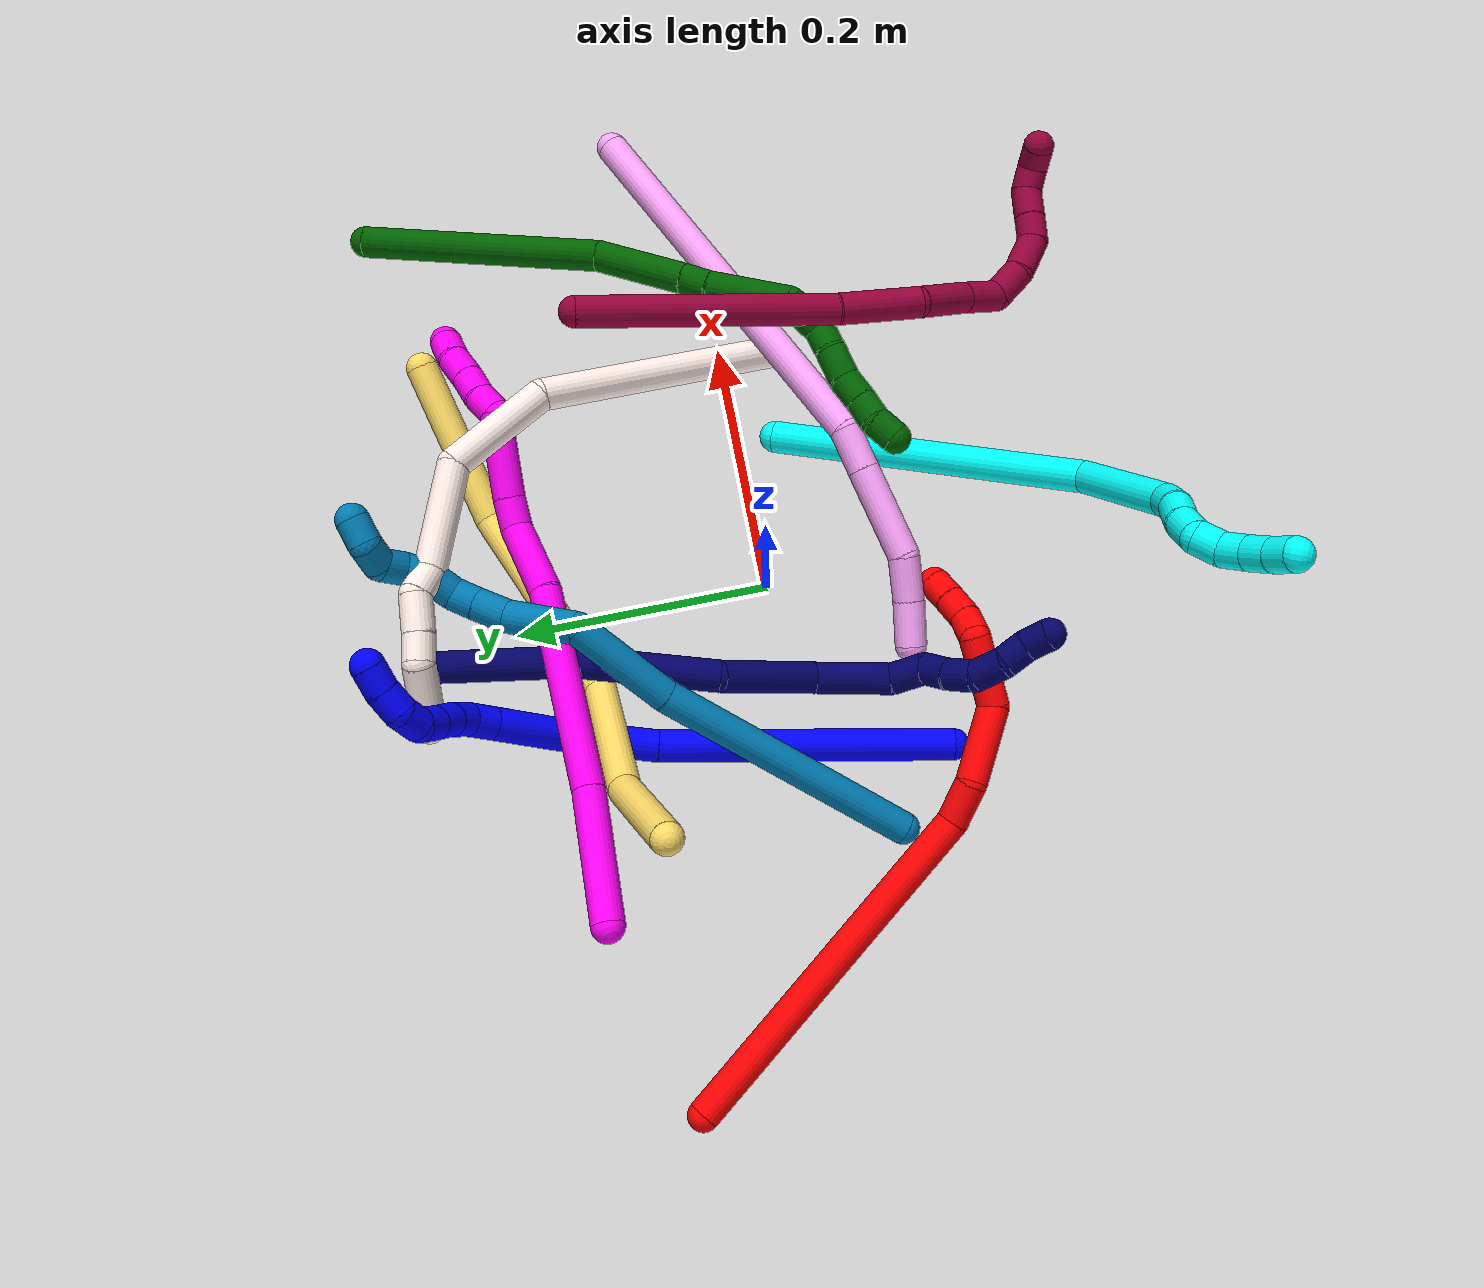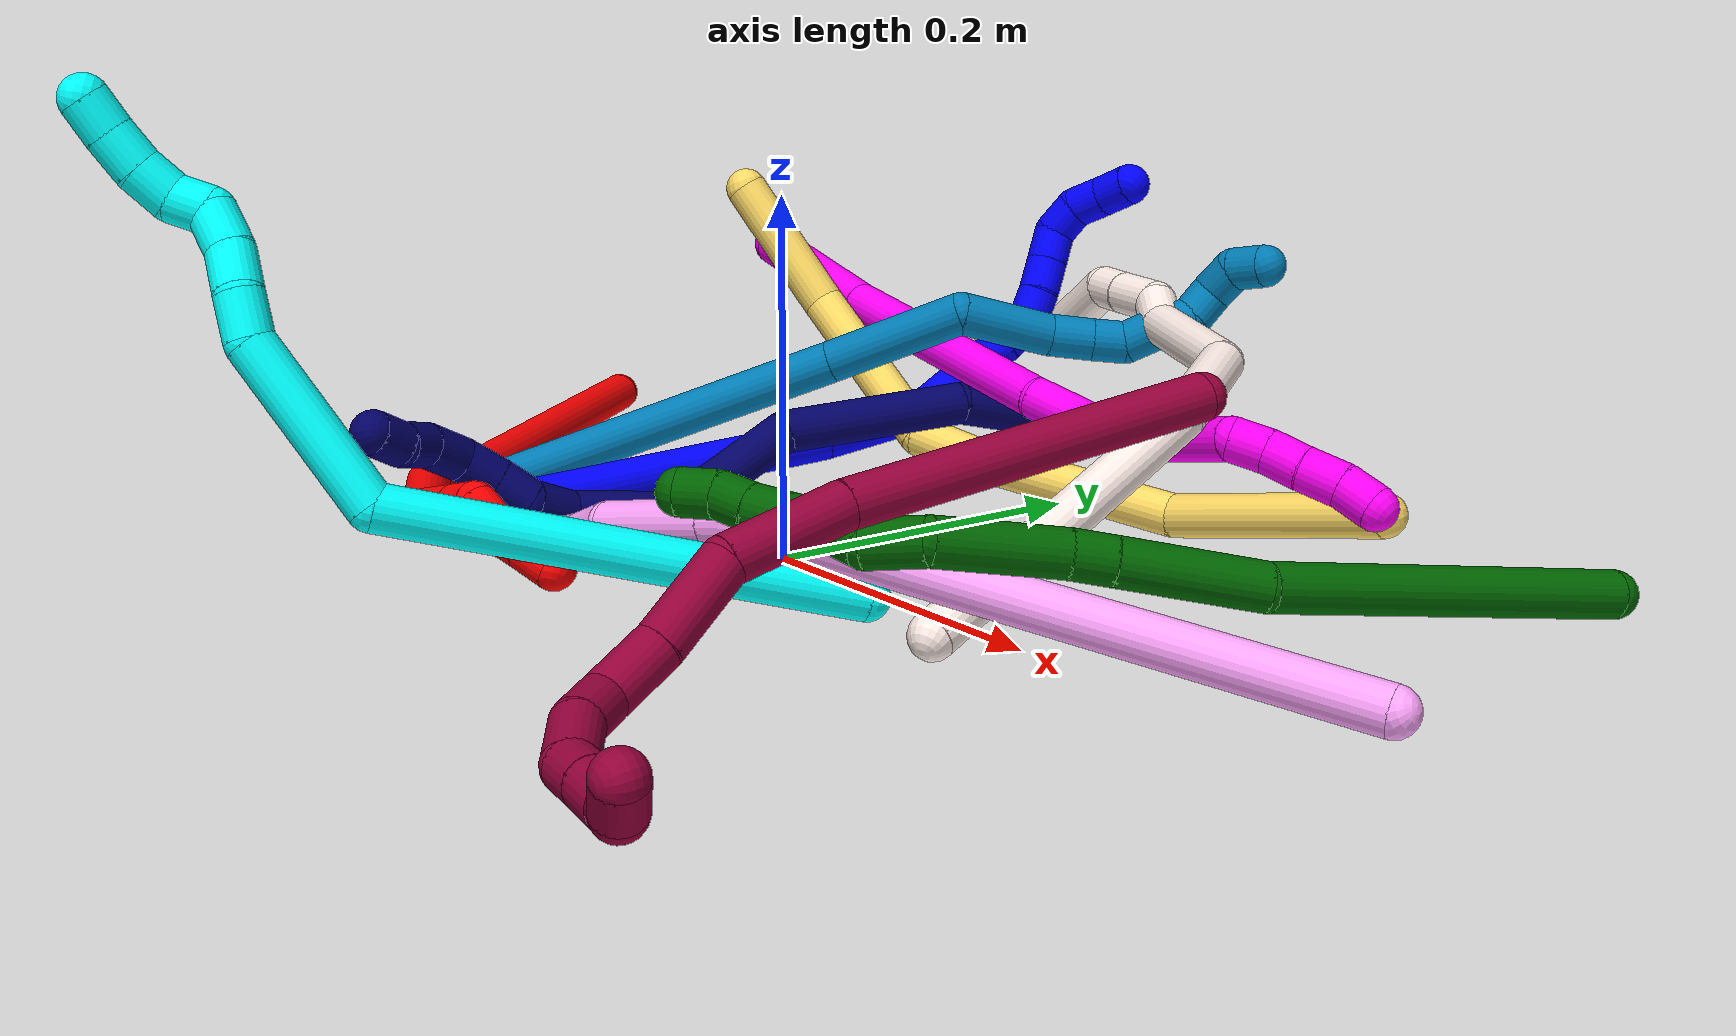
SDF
<sdf version="1.7">
 <world name="default">
  <plugin name="TubeGeneratorPlugin" filename="libtube_generator_plugin.so"/>
  <model name="photoneo_s_sensor">
   <static>1</static>
   <pose>0 0 2 1.57079 1.57079 3.14159</pose>
   <link name="link">
    <inertial><mass>0.1</mass></inertial>
    <sensor name="sensor" type="depth">
     <update_rate>30</update_rate>
     <camera>
      <horizontal_fov>1.22</horizontal_fov>
      <image><width>1920</width><height>1200</height><format>B8G8R8</format></image>
      <clip><near>0.1</near><far>4</far></clip>
      <depth_camera><output>points</output></depth_camera>
     </camera>
     <plugin name="camera_plugin" filename="libgazebo_ros_depth_camera.so">
      <baseline>0.2</baseline>
      <alwaysOn>1</alwaysOn>
      <updateRate>0.0</updateRate>
      <cameraName>camera_ir</cameraName>
      <imageTopicName>/camera/color/image_raw</imageTopicName>
      <cameraInfoTopicName>/camera/color/camera_info</cameraInfoTopicName>
      <depthImageTopicName>/camera/depth/image_raw</depthImageTopicName>
      <depthImageCameraInfoTopicName>/camera/depth/camera_info</depthImageCameraInfoTopicName>
      <pointCloudTopicName>/camera/depth/points</pointCloudTopicName>
      <frameName>fr_optical</frameName>
      <pointCloudCutoff>0.1</pointCloudCutoff>
      <pointCloudCutoffMax>2.0</pointCloudCutoffMax>
      <distortionK1>0</distortionK1>
      <distortionK2>0</distortionK2>
      <distortionK3>0</distortionK3>
      <distortionT1>0</distortionT1>
      <distortionT2>0</distortionT2>
      <CxPrime>0</CxPrime>
      <Cx>0</Cx>
      <Cy>0</Cy>
      <focalLength>0</focalLength>
      <hackBaseline>0</hackBaseline>
     </plugin>
    </sensor>
   </link>
  </model>
  <gravity>0 0 -9.8</gravity>
  <magnetic_field>6e-06 2.3e-05 -4.2e-05</magnetic_field>
  <atmosphere type="adiabatic"/>
  <physics name="default_physics" default="0" type="ode">
   <max_step_size>0.003</max_step_size>
   <real_time_factor>1</real_time_factor>
   <real_time_update_rate>1000</real_time_update_rate>
   <max_contacts>10000</max_contacts>
   <ode>
    <solver>
     <type>quick</type>
     <iters>100</iters>
     <sor>1.3</sor>
     <use_dynamic_moi_rescaling>0</use_dynamic_moi_rescaling>
    </solver>
    <constraints>
     <contact_max_correcting_vel>0</contact_max_correcting_vel>
     <contact_surface_layer>0.001</contact_surface_layer>
     <cfm>0</cfm>
     <erp>0.2</erp>
    </constraints>
   </ode>
  </physics>
  <scene><ambient>0.4 0.4 0.4 1</ambient><background>0.7 0.7 0.7 1</background><shadows>0</shadows></scene>
  <audio><device>default</device></audio>
  <spherical_coordinates>
   <surface_model>EARTH_WGS84</surface_model>
   <latitude_deg>0</latitude_deg>
   <longitude_deg>0</longitude_deg>
   <elevation>0</elevation>
   <heading_deg>0</heading_deg>
  </spherical_coordinates>
  <model name="bin">
   <static>1</static>
   <link name="bottom">
    <collision name="collision-bottom">
     <pose>0 0 -0.01 0 -0 0</pose>
     <geometry><box><size>0.8 0.6 0.02</size></box></geometry>
     <surface>
      <friction><ode><mu>100</mu><mu2>100</mu2></ode></friction>
      <contact><collide_bitmask>65535</collide_bitmask></contact>
     </surface>
    </collision>
   </link>
   <link name="west_wall">
    <collision name="collision-west_wall">
     <pose>-0.41 0 0.1 0 -0 0</pose>
     <geometry><box><size>0.02 0.6 0.2</size></box></geometry>
     <surface>
      <friction><ode><mu>100</mu><mu2>100</mu2></ode></friction>
      <contact><collide_bitmask>65535</collide_bitmask></contact>
     </surface>
    </collision>
   </link>
   <link name="east_wall">
    <collision name="collision-east_wall">
     <pose>0.41 0 0.1 0 -0 0</pose>
     <geometry><box><size>0.02 0.6 0.2</size></box></geometry>
     <surface>
      <friction><ode><mu>100</mu><mu2>100</mu2></ode></friction>
      <contact><collide_bitmask>65535</collide_bitmask></contact>
     </surface>
    </collision>
   </link>
   <link name="south_wall">
    <collision name="collision-south_wall">
     <pose>0 -0.31 0.1 0 -0 0</pose>
     <geometry><box><size>0.8 0.02 0.2</size></box></geometry>
     <surface>
      <friction><ode><mu>100</mu><mu2>100</mu2></ode></friction>
      <contact><collide_bitmask>65535</collide_bitmask></contact>
     </surface>
    </collision>
   </link>
   <link name="north_wall">
    <collision name="collision-north_wall">
     <pose>0 0.31 0.1 0 -0 0</pose>
     <geometry><box><size>0.8 0.02 0.2</size></box></geometry>
     <surface>
      <friction><ode><mu>100</mu><mu2>100</mu2></ode></friction>
      <contact><collide_bitmask>65535</collide_bitmask></contact>
     </surface>
    </collision>
   </link>
  </model>
  <model name="1">
   <static>0</static>
   <link name="1">
    <collision name="collision-cylinder-e_1_1_4">
     <pose>0.008183 0.075873 0.084236 -0.733217 0.072059 -0.027678</pose>
     <geometry><cylinder><radius>0.0125</radius><length>0.227327</length></cylinder></geometry>
     <surface>
      <friction><ode><mu>1.16</mu><mu2>1.16</mu2><slip1>0</slip1><slip2>0</slip2></ode></friction>
      <contact><ode><kp>1e+06</kp><kd>1</kd><max_vel>0</max_vel><min_depth>0.001</min_depth></ode></contact>
     </surface>
    </collision>
    <visual name="visual-cylinder-e_1_1_4">
     <pose>0.008183 0.075873 0.084236 -0.733217 0.072059 -0.027678</pose>
     <geometry><cylinder><radius>0.0125</radius><length>0.227327</length></cylinder></geometry>
     <material><ambient>0 0 1 1</ambient></material>
    </visual>
    <collision name="collision-cylinder-e_2_4_5">
     <pose>0.023645 0.172457 0.193412 -0.692995 0.22086 -0.080028</pose>
     <geometry><cylinder><radius>0.0125</radius><length>0.066451</length></cylinder></geometry>
     <surface>
      <friction><ode><mu>1.16</mu><mu2>1.16</mu2><slip1>0</slip1><slip2>0</slip2></ode></friction>
      <contact><ode><kp>1e+06</kp><kd>1</kd><max_vel>0</max_vel><min_depth>0.001</min_depth></ode></contact>
     </surface>
    </collision>
    <visual name="visual-cylinder-e_2_4_5">
     <pose>0.023645 0.172457 0.193412 -0.692995 0.22086 -0.080028</pose>
     <geometry><cylinder><radius>0.0125</radius><length>0.066451</length></cylinder></geometry>
     <material><ambient>0 0 1 1</ambient></material>
    </visual>
    <collision name="collision-cylinder-e_3_5_6">
     <pose>0.044425 0.202302 0.246713 -0.311606 0.425449 -0.067828</pose>
     <geometry><cylinder><radius>0.0125</radius><length>0.065422</length></cylinder></geometry>
     <surface>
      <friction><ode><mu>1.16</mu><mu2>1.16</mu2><slip1>0</slip1><slip2>0</slip2></ode></friction>
      <contact><ode><kp>1e+06</kp><kd>1</kd><max_vel>0</max_vel><min_depth>0.001</min_depth></ode></contact>
     </surface>
    </collision>
    <visual name="visual-cylinder-e_3_5_6">
     <pose>0.044425 0.202302 0.246713 -0.311606 0.425449 -0.067828</pose>
     <geometry><cylinder><radius>0.0125</radius><length>0.065422</length></cylinder></geometry>
     <material><ambient>0 0 1 1</ambient></material>
    </visual>
    <collision name="collision-cylinder-e_4_6_7">
     <pose>0.062314 0.213725 0.284144 -0.247089 0.43858 -0.055338</pose>
     <geometry><cylinder><radius>0.0125</radius><length>0.020666</length></cylinder></geometry>
     <surface>
      <friction><ode><mu>1.16</mu><mu2>1.16</mu2><slip1>0</slip1><slip2>0</slip2></ode></friction>
      <contact><ode><kp>1e+06</kp><kd>1</kd><max_vel>0</max_vel><min_depth>0.001</min_depth></ode></contact>
     </surface>
    </collision>
    <visual name="visual-cylinder-e_4_6_7">
     <pose>0.062314 0.213725 0.284144 -0.247089 0.43858 -0.055338</pose>
     <geometry><cylinder><radius>0.0125</radius><length>0.020666</length></cylinder></geometry>
     <material><ambient>0 0 1 1</ambient></material>
    </visual>
    <collision name="collision-cylinder-e_5_7_8">
     <pose>0.070782 0.213727 0.302064 0.252811 0.4199 0.054147</pose>
     <geometry><cylinder><radius>0.0125</radius><length>0.020018</length></cylinder></geometry>
     <surface>
      <friction><ode><mu>1.16</mu><mu2>1.16</mu2><slip1>0</slip1><slip2>0</slip2></ode></friction>
      <contact><ode><kp>1e+06</kp><kd>1</kd><max_vel>0</max_vel><min_depth>0.001</min_depth></ode></contact>
     </surface>
    </collision>
    <visual name="visual-cylinder-e_5_7_8">
     <pose>0.070782 0.213727 0.302064 0.252811 0.4199 0.054147</pose>
     <geometry><cylinder><radius>0.0125</radius><length>0.020018</length></cylinder></geometry>
     <material><ambient>0 0 1 1</ambient></material>
    </visual>
    <collision name="collision-cylinder-e_6_8_9">
     <pose>0.077902 0.208444 0.320002 0.318514 0.307542 0.049779</pose>
     <geometry><cylinder><radius>0.0125</radius><length>0.020085</length></cylinder></geometry>
     <surface>
      <friction><ode><mu>1.16</mu><mu2>1.16</mu2><slip1>0</slip1><slip2>0</slip2></ode></friction>
      <contact><ode><kp>1e+06</kp><kd>1</kd><max_vel>0</max_vel><min_depth>0.001</min_depth></ode></contact>
     </surface>
    </collision>
    <visual name="visual-cylinder-e_6_8_9">
     <pose>0.077902 0.208444 0.320002 0.318514 0.307542 0.049779</pose>
     <geometry><cylinder><radius>0.0125</radius><length>0.020085</length></cylinder></geometry>
     <material><ambient>0 0 1 1</ambient></material>
    </visual>
    <collision name="collision-cylinder-e_7_9_10">
     <pose>0.084351 0.202309 0.337958 0.340158 0.347719 0.060307</pose>
     <geometry><cylinder><radius>0.0125</radius><length>0.020006</length></cylinder></geometry>
     <surface>
      <friction><ode><mu>1.16</mu><mu2>1.16</mu2><slip1>0</slip1><slip2>0</slip2></ode></friction>
      <contact><ode><kp>1e+06</kp><kd>1</kd><max_vel>0</max_vel><min_depth>0.001</min_depth></ode></contact>
     </surface>
    </collision>
    <visual name="visual-cylinder-e_7_9_10">
     <pose>0.084351 0.202309 0.337958 0.340158 0.347719 0.060307</pose>
     <geometry><cylinder><radius>0.0125</radius><length>0.020006</length></cylinder></geometry>
     <material><ambient>0 0 1 1</ambient></material>
    </visual>
    <collision name="collision-cylinder-e_8_10_11">
     <pose>0.095173 0.199823 0.353508 -0.097175 0.834697 -0.043114</pose>
     <geometry><cylinder><radius>0.0125</radius><length>0.020007</length></cylinder></geometry>
     <surface>
      <friction><ode><mu>1.16</mu><mu2>1.16</mu2><slip1>0</slip1><slip2>0</slip2></ode></friction>
      <contact><ode><kp>1e+06</kp><kd>1</kd><max_vel>0</max_vel><min_depth>0.001</min_depth></ode></contact>
     </surface>
    </collision>
    <visual name="visual-cylinder-e_8_10_11">
     <pose>0.095173 0.199823 0.353508 -0.097175 0.834697 -0.043114</pose>
     <geometry><cylinder><radius>0.0125</radius><length>0.020007</length></cylinder></geometry>
     <material><ambient>0 0 1 1</ambient></material>
    </visual>
    <collision name="collision-cylinder-e_9_11_12">
     <pose>0.110836 0.204952 0.363649 -0.91335 0.96976 -0.50656</pose>
     <geometry><cylinder><radius>0.0125</radius><length>0.020003</length></cylinder></geometry>
     <surface>
      <friction><ode><mu>1.16</mu><mu2>1.16</mu2><slip1>0</slip1><slip2>0</slip2></ode></friction>
      <contact><ode><kp>1e+06</kp><kd>1</kd><max_vel>0</max_vel><min_depth>0.001</min_depth></ode></contact>
     </surface>
    </collision>
    <visual name="visual-cylinder-e_9_11_12">
     <pose>0.110836 0.204952 0.363649 -0.91335 0.96976 -0.50656</pose>
     <geometry><cylinder><radius>0.0125</radius><length>0.020003</length></cylinder></geometry>
     <material><ambient>0 0 1 1</ambient></material>
    </visual>
    <collision name="collision-cylinder-e_10_12_2">
     <pose>0.128168 0.213078 0.369181 -1.05378 1.13782 -0.712255</pose>
     <geometry><cylinder><radius>0.0125</radius><length>0.020014</length></cylinder></geometry>
     <surface>
      <friction><ode><mu>1.16</mu><mu2>1.16</mu2><slip1>0</slip1><slip2>0</slip2></ode></friction>
      <contact><ode><kp>1e+06</kp><kd>1</kd><max_vel>0</max_vel><min_depth>0.001</min_depth></ode></contact>
     </surface>
    </collision>
    <visual name="visual-cylinder-e_10_12_2">
     <pose>0.128168 0.213078 0.369181 -1.05378 1.13782 -0.712255</pose>
     <geometry><cylinder><radius>0.0125</radius><length>0.020014</length></cylinder></geometry>
     <material><ambient>0 0 1 1</ambient></material>
    </visual>
    <collision name="collision-sphere-2">
     <pose>0.137252 0.216728 0.371256 0 -0 0</pose>
     <geometry><sphere><radius>0.0125</radius></sphere></geometry>
     <surface>
      <friction><ode><mu>1.16</mu><mu2>1.16</mu2><slip1>0</slip1><slip2>0</slip2></ode></friction>
      <contact><ode><kp>1e+06</kp><kd>1</kd><max_vel>0</max_vel><min_depth>0.001</min_depth></ode></contact>
     </surface>
    </collision>
    <visual name="visual-sphere-2">
     <pose>0.137252 0.216728 0.371256 0 -0 0</pose>
     <geometry><sphere><radius>0.0125</radius></sphere></geometry>
     <material><ambient>0 0 1 1</ambient></material>
    </visual>
    <collision name="collision-sphere-12">
     <pose>0.119085 0.209429 0.367106 0 -0 0</pose>
     <geometry><sphere><radius>0.0125</radius></sphere></geometry>
     <surface>
      <friction><ode><mu>1.16</mu><mu2>1.16</mu2><slip1>0</slip1><slip2>0</slip2></ode></friction>
      <contact><ode><kp>1e+06</kp><kd>1</kd><max_vel>0</max_vel><min_depth>0.001</min_depth></ode></contact>
     </surface>
    </collision>
    <visual name="visual-sphere-12">
     <pose>0.119085 0.209429 0.367106 0 -0 0</pose>
     <geometry><sphere><radius>0.0125</radius></sphere></geometry>
     <material><ambient>0 0 1 1</ambient></material>
    </visual>
    <collision name="collision-sphere-11">
     <pose>0.102587 0.200475 0.360193 0 -0 0</pose>
     <geometry><sphere><radius>0.0125</radius></sphere></geometry>
     <surface>
      <friction><ode><mu>1.16</mu><mu2>1.16</mu2><slip1>0</slip1><slip2>0</slip2></ode></friction>
      <contact><ode><kp>1e+06</kp><kd>1</kd><max_vel>0</max_vel><min_depth>0.001</min_depth></ode></contact>
     </surface>
    </collision>
    <visual name="visual-sphere-11">
     <pose>0.102587 0.200475 0.360193 0 -0 0</pose>
     <geometry><sphere><radius>0.0125</radius></sphere></geometry>
     <material><ambient>0 0 1 1</ambient></material>
    </visual>
    <collision name="collision-sphere-10">
     <pose>0.087759 0.199171 0.346823 0 -0 0</pose>
     <geometry><sphere><radius>0.0125</radius></sphere></geometry>
     <surface>
      <friction><ode><mu>1.16</mu><mu2>1.16</mu2><slip1>0</slip1><slip2>0</slip2></ode></friction>
      <contact><ode><kp>1e+06</kp><kd>1</kd><max_vel>0</max_vel><min_depth>0.001</min_depth></ode></contact>
     </surface>
    </collision>
    <visual name="visual-sphere-10">
     <pose>0.087759 0.199171 0.346823 0 -0 0</pose>
     <geometry><sphere><radius>0.0125</radius></sphere></geometry>
     <material><ambient>0 0 1 1</ambient></material>
    </visual>
    <collision name="collision-sphere-9">
     <pose>0.080942 0.205447 0.329092 0 -0 0</pose>
     <geometry><sphere><radius>0.0125</radius></sphere></geometry>
     <surface>
      <friction><ode><mu>1.16</mu><mu2>1.16</mu2><slip1>0</slip1><slip2>0</slip2></ode></friction>
      <contact><ode><kp>1e+06</kp><kd>1</kd><max_vel>0</max_vel><min_depth>0.001</min_depth></ode></contact>
     </surface>
    </collision>
    <visual name="visual-sphere-9">
     <pose>0.080942 0.205447 0.329092 0 -0 0</pose>
     <geometry><sphere><radius>0.0125</radius></sphere></geometry>
     <material><ambient>0 0 1 1</ambient></material>
    </visual>
    <collision name="collision-sphere-4">
     <pose>0.016367 0.151747 0.168471 0 -0 0</pose>
     <geometry><sphere><radius>0.0125</radius></sphere></geometry>
     <surface>
      <friction><ode><mu>1.16</mu><mu2>1.16</mu2><slip1>0</slip1><slip2>0</slip2></ode></friction>
      <contact><ode><kp>1e+06</kp><kd>1</kd><max_vel>0</max_vel><min_depth>0.001</min_depth></ode></contact>
     </surface>
    </collision>
    <visual name="visual-sphere-4">
     <pose>0.016367 0.151747 0.168471 0 -0 0</pose>
     <geometry><sphere><radius>0.0125</radius></sphere></geometry>
     <material><ambient>0 0 1 1</ambient></material>
    </visual>
    <collision name="collision-sphere-1">
     <geometry><sphere><radius>0.0125</radius></sphere></geometry>
     <surface>
      <friction><ode><mu>1.16</mu><mu2>1.16</mu2><slip1>0</slip1><slip2>0</slip2></ode></friction>
      <contact><ode><kp>1e+06</kp><kd>1</kd><max_vel>0</max_vel><min_depth>0.001</min_depth></ode></contact>
     </surface>
    </collision>
    <visual name="visual-sphere-1">
     <geometry><sphere><radius>0.0125</radius></sphere></geometry>
     <material><ambient>0 0 1 1</ambient></material>
    </visual>
    <collision name="collision-sphere-8">
     <pose>0.074862 0.211441 0.310913 0 -0 0</pose>
     <geometry><sphere><radius>0.0125</radius></sphere></geometry>
     <surface>
      <friction><ode><mu>1.16</mu><mu2>1.16</mu2><slip1>0</slip1><slip2>0</slip2></ode></friction>
      <contact><ode><kp>1e+06</kp><kd>1</kd><max_vel>0</max_vel><min_depth>0.001</min_depth></ode></contact>
     </surface>
    </collision>
    <visual name="visual-sphere-8">
     <pose>0.074862 0.211441 0.310913 0 -0 0</pose>
     <geometry><sphere><radius>0.0125</radius></sphere></geometry>
     <material><ambient>0 0 1 1</ambient></material>
    </visual>
    <collision name="collision-sphere-5">
     <pose>0.030924 0.193168 0.218353 0 -0 0</pose>
     <geometry><sphere><radius>0.0125</radius></sphere></geometry>
     <surface>
      <friction><ode><mu>1.16</mu><mu2>1.16</mu2><slip1>0</slip1><slip2>0</slip2></ode></friction>
      <contact><ode><kp>1e+06</kp><kd>1</kd><max_vel>0</max_vel><min_depth>0.001</min_depth></ode></contact>
     </surface>
    </collision>
    <visual name="visual-sphere-5">
     <pose>0.030924 0.193168 0.218353 0 -0 0</pose>
     <geometry><sphere><radius>0.0125</radius></sphere></geometry>
     <material><ambient>0 0 1 1</ambient></material>
    </visual>
    <collision name="collision-sphere-6">
     <pose>0.057926 0.211437 0.275073 0 -0 0</pose>
     <geometry><sphere><radius>0.0125</radius></sphere></geometry>
     <surface>
      <friction><ode><mu>1.16</mu><mu2>1.16</mu2><slip1>0</slip1><slip2>0</slip2></ode></friction>
      <contact><ode><kp>1e+06</kp><kd>1</kd><max_vel>0</max_vel><min_depth>0.001</min_depth></ode></contact>
     </surface>
    </collision>
    <visual name="visual-sphere-6">
     <pose>0.057926 0.211437 0.275073 0 -0 0</pose>
     <geometry><sphere><radius>0.0125</radius></sphere></geometry>
     <material><ambient>0 0 1 1</ambient></material>
    </visual>
    <collision name="collision-sphere-7">
     <pose>0.066702 0.216013 0.293215 0 -0 0</pose>
     <geometry><sphere><radius>0.0125</radius></sphere></geometry>
     <surface>
      <friction><ode><mu>1.16</mu><mu2>1.16</mu2><slip1>0</slip1><slip2>0</slip2></ode></friction>
      <contact><ode><kp>1e+06</kp><kd>1</kd><max_vel>0</max_vel><min_depth>0.001</min_depth></ode></contact>
     </surface>
    </collision>
    <visual name="visual-sphere-7">
     <pose>0.066702 0.216013 0.293215 0 -0 0</pose>
     <geometry><sphere><radius>0.0125</radius></sphere></geometry>
     <material><ambient>0 0 1 1</ambient></material>
    </visual>
    <inertial>
     <pose>0.037963 0.142469 0.18997 0 -0 0</pose>
     <mass>0.5</mass>
     <inertia>
      <ixx>0.001021</ixx>
      <ixy>0</ixy>
      <ixz>0</ixz>
      <iyy>0.000776</iyy>
      <iyz>0</iyz>
      <izz>-0.000748</izz>
     </inertia>
    </inertial>
   </link>
   <pose>-0.152555 -0.115371 0.01149 -0.778622 -0.600688 -0.158133</pose>
  </model>
  <model name="2">
   <static>0</static>
   <link name="2">
    <collision name="collision-cylinder-e_1_1_4">
     <pose>0.045901 -0.094089 -0.097689 2.37496 0.326324 0.775167</pose>
     <geometry><cylinder><radius>0.0125</radius><length>0.286376</length></cylinder></geometry>
     <surface>
      <friction><ode><mu>1.16</mu><mu2>1.16</mu2><slip1>0</slip1><slip2>0</slip2></ode></friction>
      <contact><ode><kp>1e+06</kp><kd>1</kd><max_vel>0</max_vel><min_depth>0.001</min_depth></ode></contact>
     </surface>
    </collision>
    <visual name="visual-cylinder-e_1_1_4">
     <pose>0.045901 -0.094089 -0.097689 2.37496 0.326324 0.775167</pose>
     <geometry><cylinder><radius>0.0125</radius><length>0.286376</length></cylinder></geometry>
     <material><ambient>1 0 0 1</ambient></material>
    </visual>
    <collision name="collision-cylinder-e_2_4_5">
     <pose>0.102483 -0.200155 -0.201365 2.03438 0.67334 1.03049</pose>
     <geometry><cylinder><radius>0.0125</radius><length>0.034256</length></cylinder></geometry>
     <surface>
      <friction><ode><mu>1.16</mu><mu2>1.16</mu2><slip1>0</slip1><slip2>0</slip2></ode></friction>
      <contact><ode><kp>1e+06</kp><kd>1</kd><max_vel>0</max_vel><min_depth>0.001</min_depth></ode></contact>
     </surface>
    </collision>
    <visual name="visual-cylinder-e_2_4_5">
     <pose>0.102483 -0.200155 -0.201365 2.03438 0.67334 1.03049</pose>
     <geometry><cylinder><radius>0.0125</radius><length>0.034256</length></cylinder></geometry>
     <material><ambient>1 0 0 1</ambient></material>
    </visual>
    <collision name="collision-cylinder-e_3_5_6">
     <pose>0.133027 -0.224655 -0.227207 2.57888 0.702252 1.80557</pose>
     <geometry><cylinder><radius>0.0125</radius><length>0.061501</length></cylinder></geometry>
     <surface>
      <friction><ode><mu>1.16</mu><mu2>1.16</mu2><slip1>0</slip1><slip2>0</slip2></ode></friction>
      <contact><ode><kp>1e+06</kp><kd>1</kd><max_vel>0</max_vel><min_depth>0.001</min_depth></ode></contact>
     </surface>
    </collision>
    <visual name="visual-cylinder-e_3_5_6">
     <pose>0.133027 -0.224655 -0.227207 2.57888 0.702252 1.80557</pose>
     <geometry><cylinder><radius>0.0125</radius><length>0.061501</length></cylinder></geometry>
     <material><ambient>1 0 0 1</ambient></material>
    </visual>
    <collision name="collision-cylinder-e_4_6_7">
     <pose>0.169784 -0.239339 -0.25049 2.57929 1.3354 2.43942</pose>
     <geometry><cylinder><radius>0.0125</radius><length>0.034748</length></cylinder></geometry>
     <surface>
      <friction><ode><mu>1.16</mu><mu2>1.16</mu2><slip1>0</slip1><slip2>0</slip2></ode></friction>
      <contact><ode><kp>1e+06</kp><kd>1</kd><max_vel>0</max_vel><min_depth>0.001</min_depth></ode></contact>
     </surface>
    </collision>
    <visual name="visual-cylinder-e_4_6_7">
     <pose>0.169784 -0.239339 -0.25049 2.57929 1.3354 2.43942</pose>
     <geometry><cylinder><radius>0.0125</radius><length>0.034748</length></cylinder></geometry>
     <material><ambient>1 0 0 1</ambient></material>
    </visual>
    <collision name="collision-cylinder-e_5_7_8">
     <pose>0.19702 -0.242831 -0.256016 2.57582 1.33498 2.43493</pose>
     <geometry><cylinder><radius>0.0125</radius><length>0.021271</length></cylinder></geometry>
     <surface>
      <friction><ode><mu>1.16</mu><mu2>1.16</mu2><slip1>0</slip1><slip2>0</slip2></ode></friction>
      <contact><ode><kp>1e+06</kp><kd>1</kd><max_vel>0</max_vel><min_depth>0.001</min_depth></ode></contact>
     </surface>
    </collision>
    <visual name="visual-cylinder-e_5_7_8">
     <pose>0.19702 -0.242831 -0.256016 2.57582 1.33498 2.43493</pose>
     <geometry><cylinder><radius>0.0125</radius><length>0.021271</length></cylinder></geometry>
     <material><ambient>1 0 0 1</ambient></material>
    </visual>
    <collision name="collision-cylinder-e_6_8_9">
     <pose>0.214068 -0.240494 -0.265174 -2.66228 0.700358 -1.9623</pose>
     <geometry><cylinder><radius>0.0125</radius><length>0.020812</length></cylinder></geometry>
     <surface>
      <friction><ode><mu>1.16</mu><mu2>1.16</mu2><slip1>0</slip1><slip2>0</slip2></ode></friction>
      <contact><ode><kp>1e+06</kp><kd>1</kd><max_vel>0</max_vel><min_depth>0.001</min_depth></ode></contact>
     </surface>
    </collision>
    <visual name="visual-cylinder-e_6_8_9">
     <pose>0.214068 -0.240494 -0.265174 -2.66228 0.700358 -1.9623</pose>
     <geometry><cylinder><radius>0.0125</radius><length>0.020812</length></cylinder></geometry>
     <material><ambient>1 0 0 1</ambient></material>
    </visual>
    <collision name="collision-cylinder-e_7_9_10">
     <pose>0.228405 -0.231829 -0.276976 -2.33021 0.836503 -1.60503</pose>
     <geometry><cylinder><radius>0.0125</radius><length>0.020559</length></cylinder></geometry>
     <surface>
      <friction><ode><mu>1.16</mu><mu2>1.16</mu2><slip1>0</slip1><slip2>0</slip2></ode></friction>
      <contact><ode><kp>1e+06</kp><kd>1</kd><max_vel>0</max_vel><min_depth>0.001</min_depth></ode></contact>
     </surface>
    </collision>
    <visual name="visual-cylinder-e_7_9_10">
     <pose>0.228405 -0.231829 -0.276976 -2.33021 0.836503 -1.60503</pose>
     <geometry><cylinder><radius>0.0125</radius><length>0.020559</length></cylinder></geometry>
     <material><ambient>1 0 0 1</ambient></material>
    </visual>
    <collision name="collision-cylinder-e_8_10_2">
     <pose>0.24326 -0.22145 -0.286582 -2.30548 0.783294 -1.4979</pose>
     <geometry><cylinder><radius>0.0125</radius><length>0.020477</length></cylinder></geometry>
     <surface>
      <friction><ode><mu>1.16</mu><mu2>1.16</mu2><slip1>0</slip1><slip2>0</slip2></ode></friction>
      <contact><ode><kp>1e+06</kp><kd>1</kd><max_vel>0</max_vel><min_depth>0.001</min_depth></ode></contact>
     </surface>
    </collision>
    <visual name="visual-cylinder-e_8_10_2">
     <pose>0.24326 -0.22145 -0.286582 -2.30548 0.783294 -1.4979</pose>
     <geometry><cylinder><radius>0.0125</radius><length>0.020477</length></cylinder></geometry>
     <material><ambient>1 0 0 1</ambient></material>
    </visual>
    <collision name="collision-sphere-2">
     <pose>0.250485 -0.216067 -0.291445 0 -0 0</pose>
     <geometry><sphere><radius>0.0125</radius></sphere></geometry>
     <surface>
      <friction><ode><mu>1.16</mu><mu2>1.16</mu2><slip1>0</slip1><slip2>0</slip2></ode></friction>
      <contact><ode><kp>1e+06</kp><kd>1</kd><max_vel>0</max_vel><min_depth>0.001</min_depth></ode></contact>
     </surface>
    </collision>
    <visual name="visual-sphere-2">
     <pose>0.250485 -0.216067 -0.291445 0 -0 0</pose>
     <geometry><sphere><radius>0.0125</radius></sphere></geometry>
     <material><ambient>1 0 0 1</ambient></material>
    </visual>
    <collision name="collision-sphere-10">
     <pose>0.236035 -0.226834 -0.281718 0 -0 0</pose>
     <geometry><sphere><radius>0.0125</radius></sphere></geometry>
     <surface>
      <friction><ode><mu>1.16</mu><mu2>1.16</mu2><slip1>0</slip1><slip2>0</slip2></ode></friction>
      <contact><ode><kp>1e+06</kp><kd>1</kd><max_vel>0</max_vel><min_depth>0.001</min_depth></ode></contact>
     </surface>
    </collision>
    <visual name="visual-sphere-10">
     <pose>0.236035 -0.226834 -0.281718 0 -0 0</pose>
     <geometry><sphere><radius>0.0125</radius></sphere></geometry>
     <material><ambient>1 0 0 1</ambient></material>
    </visual>
    <collision name="collision-sphere-9">
     <pose>0.220775 -0.236824 -0.272234 0 -0 0</pose>
     <geometry><sphere><radius>0.0125</radius></sphere></geometry>
     <surface>
      <friction><ode><mu>1.16</mu><mu2>1.16</mu2><slip1>0</slip1><slip2>0</slip2></ode></friction>
      <contact><ode><kp>1e+06</kp><kd>1</kd><max_vel>0</max_vel><min_depth>0.001</min_depth></ode></contact>
     </surface>
    </collision>
    <visual name="visual-sphere-9">
     <pose>0.220775 -0.236824 -0.272234 0 -0 0</pose>
     <geometry><sphere><radius>0.0125</radius></sphere></geometry>
     <material><ambient>1 0 0 1</ambient></material>
    </visual>
    <collision name="collision-sphere-4">
     <pose>0.091802 -0.188179 -0.195377 0 -0 0</pose>
     <geometry><sphere><radius>0.0125</radius></sphere></geometry>
     <surface>
      <friction><ode><mu>1.16</mu><mu2>1.16</mu2><slip1>0</slip1><slip2>0</slip2></ode></friction>
      <contact><ode><kp>1e+06</kp><kd>1</kd><max_vel>0</max_vel><min_depth>0.001</min_depth></ode></contact>
     </surface>
    </collision>
    <visual name="visual-sphere-4">
     <pose>0.091802 -0.188179 -0.195377 0 -0 0</pose>
     <geometry><sphere><radius>0.0125</radius></sphere></geometry>
     <material><ambient>1 0 0 1</ambient></material>
    </visual>
    <collision name="collision-sphere-1">
     <geometry><sphere><radius>0.0125</radius></sphere></geometry>
     <surface>
      <friction><ode><mu>1.16</mu><mu2>1.16</mu2><slip1>0</slip1><slip2>0</slip2></ode></friction>
      <contact><ode><kp>1e+06</kp><kd>1</kd><max_vel>0</max_vel><min_depth>0.001</min_depth></ode></contact>
     </surface>
    </collision>
    <visual name="visual-sphere-1">
     <geometry><sphere><radius>0.0125</radius></sphere></geometry>
     <material><ambient>1 0 0 1</ambient></material>
    </visual>
    <collision name="collision-sphere-8">
     <pose>0.207361 -0.244163 -0.258114 0 -0 0</pose>
     <geometry><sphere><radius>0.0125</radius></sphere></geometry>
     <surface>
      <friction><ode><mu>1.16</mu><mu2>1.16</mu2><slip1>0</slip1><slip2>0</slip2></ode></friction>
      <contact><ode><kp>1e+06</kp><kd>1</kd><max_vel>0</max_vel><min_depth>0.001</min_depth></ode></contact>
     </surface>
    </collision>
    <visual name="visual-sphere-8">
     <pose>0.207361 -0.244163 -0.258114 0 -0 0</pose>
     <geometry><sphere><radius>0.0125</radius></sphere></geometry>
     <material><ambient>1 0 0 1</ambient></material>
    </visual>
    <collision name="collision-sphere-5">
     <pose>0.113164 -0.212132 -0.207352 0 -0 0</pose>
     <geometry><sphere><radius>0.0125</radius></sphere></geometry>
     <surface>
      <friction><ode><mu>1.16</mu><mu2>1.16</mu2><slip1>0</slip1><slip2>0</slip2></ode></friction>
      <contact><ode><kp>1e+06</kp><kd>1</kd><max_vel>0</max_vel><min_depth>0.001</min_depth></ode></contact>
     </surface>
    </collision>
    <visual name="visual-sphere-5">
     <pose>0.113164 -0.212132 -0.207352 0 -0 0</pose>
     <geometry><sphere><radius>0.0125</radius></sphere></geometry>
     <material><ambient>1 0 0 1</ambient></material>
    </visual>
    <collision name="collision-sphere-6">
     <pose>0.152889 -0.237179 -0.247062 0 -0 0</pose>
     <geometry><sphere><radius>0.0125</radius></sphere></geometry>
     <surface>
      <friction><ode><mu>1.16</mu><mu2>1.16</mu2><slip1>0</slip1><slip2>0</slip2></ode></friction>
      <contact><ode><kp>1e+06</kp><kd>1</kd><max_vel>0</max_vel><min_depth>0.001</min_depth></ode></contact>
     </surface>
    </collision>
    <visual name="visual-sphere-6">
     <pose>0.152889 -0.237179 -0.247062 0 -0 0</pose>
     <geometry><sphere><radius>0.0125</radius></sphere></geometry>
     <material><ambient>1 0 0 1</ambient></material>
    </visual>
    <collision name="collision-sphere-7">
     <pose>0.186679 -0.241499 -0.253918 0 -0 0</pose>
     <geometry><sphere><radius>0.0125</radius></sphere></geometry>
     <surface>
      <friction><ode><mu>1.16</mu><mu2>1.16</mu2><slip1>0</slip1><slip2>0</slip2></ode></friction>
      <contact><ode><kp>1e+06</kp><kd>1</kd><max_vel>0</max_vel><min_depth>0.001</min_depth></ode></contact>
     </surface>
    </collision>
    <visual name="visual-sphere-7">
     <pose>0.186679 -0.241499 -0.253918 0 -0 0</pose>
     <geometry><sphere><radius>0.0125</radius></sphere></geometry>
     <material><ambient>1 0 0 1</ambient></material>
    </visual>
    <inertial>
     <pose>0.098119 -0.150812 -0.160157 0 -0 0</pose>
     <mass>0.5</mass>
     <inertia><ixx>0.00267</ixx><ixy>0</ixy><ixz>0</ixz><iyy>0.00062</iyy><iyz>0</iyz><izz>0.000624</izz></inertia>
    </inertial>
   </link>
   <pose>-0.384893 0.125845 0.01246 -0.677819 -0.346715 0.304319</pose>
  </model>
  <model name="3">
   <static>0</static>
   <link name="3">
    <collision name="collision-cylinder-e_1_1_4">
     <pose>-0.005545 0.000833 0.124143 -0.006708 -0.044636 0.00015</pose>
     <geometry><cylinder><radius>0.0125</radius><length>0.248539</length></cylinder></geometry>
     <surface>
      <friction><ode><mu>1.16</mu><mu2>1.16</mu2><slip1>0</slip1><slip2>0</slip2></ode></friction>
      <contact><ode><kp>1e+06</kp><kd>1</kd><max_vel>0</max_vel><min_depth>0.001</min_depth></ode></contact>
     </surface>
    </collision>
    <visual name="visual-cylinder-e_1_1_4">
     <pose>-0.005545 0.000833 0.124143 -0.006708 -0.044636 0.00015</pose>
     <geometry><cylinder><radius>0.0125</radius><length>0.248539</length></cylinder></geometry>
     <material><ambient>0.003922 1 0.996078 1</ambient></material>
    </visual>
    <collision name="collision-cylinder-e_2_4_5">
     <pose>-0.018086 -0.031378 0.282933 0.761704 -0.145101 -0.058184</pose>
     <geometry><cylinder><radius>0.0125</radius><length>0.096773</length></cylinder></geometry>
     <surface>
      <friction><ode><mu>1.16</mu><mu2>1.16</mu2><slip1>0</slip1><slip2>0</slip2></ode></friction>
      <contact><ode><kp>1e+06</kp><kd>1</kd><max_vel>0</max_vel><min_depth>0.001</min_depth></ode></contact>
     </surface>
    </collision>
    <visual name="visual-cylinder-e_2_4_5">
     <pose>-0.018086 -0.031378 0.282933 0.761704 -0.145101 -0.058184</pose>
     <geometry><cylinder><radius>0.0125</radius><length>0.096773</length></cylinder></geometry>
     <material><ambient>0.003922 1 0.996078 1</ambient></material>
    </visual>
    <collision name="collision-cylinder-e_3_5_6">
     <pose>-0.026798 -0.075691 0.322273 1.17625 -0.139624 -0.093191</pose>
     <geometry><cylinder><radius>0.0125</radius><length>0.024656</length></cylinder></geometry>
     <surface>
      <friction><ode><mu>1.16</mu><mu2>1.16</mu2><slip1>0</slip1><slip2>0</slip2></ode></friction>
      <contact><ode><kp>1e+06</kp><kd>1</kd><max_vel>0</max_vel><min_depth>0.001</min_depth></ode></contact>
     </surface>
    </collision>
    <visual name="visual-cylinder-e_3_5_6">
     <pose>-0.026798 -0.075691 0.322273 1.17625 -0.139624 -0.093191</pose>
     <geometry><cylinder><radius>0.0125</radius><length>0.024656</length></cylinder></geometry>
     <material><ambient>0.003922 1 0.996078 1</ambient></material>
    </visual>
    <collision name="collision-cylinder-e_4_6_7">
     <pose>-0.027043 -0.098331 0.330921 1.23601 0.121561 0.08647</pose>
     <geometry><cylinder><radius>0.0125</radius><length>0.024256</length></cylinder></geometry>
     <surface>
      <friction><ode><mu>1.16</mu><mu2>1.16</mu2><slip1>0</slip1><slip2>0</slip2></ode></friction>
      <contact><ode><kp>1e+06</kp><kd>1</kd><max_vel>0</max_vel><min_depth>0.001</min_depth></ode></contact>
     </surface>
    </collision>
    <visual name="visual-cylinder-e_4_6_7">
     <pose>-0.027043 -0.098331 0.330921 1.23601 0.121561 0.08647</pose>
     <geometry><cylinder><radius>0.0125</radius><length>0.024256</length></cylinder></geometry>
     <material><ambient>0.003922 1 0.996078 1</ambient></material>
    </visual>
    <collision name="collision-cylinder-e_5_7_8">
     <pose>-0.02463 -0.11956 0.341117 1.00643 0.080607 0.04439</pose>
     <geometry><cylinder><radius>0.0125</radius><length>0.023412</length></cylinder></geometry>
     <surface>
      <friction><ode><mu>1.16</mu><mu2>1.16</mu2><slip1>0</slip1><slip2>0</slip2></ode></friction>
      <contact><ode><kp>1e+06</kp><kd>1</kd><max_vel>0</max_vel><min_depth>0.001</min_depth></ode></contact>
     </surface>
    </collision>
    <visual name="visual-cylinder-e_5_7_8">
     <pose>-0.02463 -0.11956 0.341117 1.00643 0.080607 0.04439</pose>
     <geometry><cylinder><radius>0.0125</radius><length>0.023412</length></cylinder></geometry>
     <material><ambient>0.003922 1 0.996078 1</ambient></material>
    </visual>
    <collision name="collision-cylinder-e_6_8_9">
     <pose>-0.021752 -0.131891 0.356952 0.252169 0.19291 0.024528</pose>
     <geometry><cylinder><radius>0.0125</radius><length>0.020189</length></cylinder></geometry>
     <surface>
      <friction><ode><mu>1.16</mu><mu2>1.16</mu2><slip1>0</slip1><slip2>0</slip2></ode></friction>
      <contact><ode><kp>1e+06</kp><kd>1</kd><max_vel>0</max_vel><min_depth>0.001</min_depth></ode></contact>
     </surface>
    </collision>
    <visual name="visual-cylinder-e_6_8_9">
     <pose>-0.021752 -0.131891 0.356952 0.252169 0.19291 0.024528</pose>
     <geometry><cylinder><radius>0.0125</radius><length>0.020189</length></cylinder></geometry>
     <material><ambient>0.003922 1 0.996078 1</ambient></material>
    </visual>
    <collision name="collision-cylinder-e_7_9_10">
     <pose>-0.021934 -0.139175 0.375521 0.492141 -0.205007 -0.051659</pose>
     <geometry><cylinder><radius>0.0125</radius><length>0.020803</length></cylinder></geometry>
     <surface>
      <friction><ode><mu>1.16</mu><mu2>1.16</mu2><slip1>0</slip1><slip2>0</slip2></ode></friction>
      <contact><ode><kp>1e+06</kp><kd>1</kd><max_vel>0</max_vel><min_depth>0.001</min_depth></ode></contact>
     </surface>
    </collision>
    <visual name="visual-cylinder-e_7_9_10">
     <pose>-0.021934 -0.139175 0.375521 0.492141 -0.205007 -0.051659</pose>
     <geometry><cylinder><radius>0.0125</radius><length>0.020803</length></cylinder></geometry>
     <material><ambient>0.003922 1 0.996078 1</ambient></material>
    </visual>
    <collision name="collision-cylinder-e_8_10_11">
     <pose>-0.027076 -0.150206 0.392619 0.653467 -0.287368 -0.09798</pose>
     <geometry><cylinder><radius>0.0125</radius><length>0.021335</length></cylinder></geometry>
     <surface>
      <friction><ode><mu>1.16</mu><mu2>1.16</mu2><slip1>0</slip1><slip2>0</slip2></ode></friction>
      <contact><ode><kp>1e+06</kp><kd>1</kd><max_vel>0</max_vel><min_depth>0.001</min_depth></ode></contact>
     </surface>
    </collision>
    <visual name="visual-cylinder-e_8_10_11">
     <pose>-0.027076 -0.150206 0.392619 0.653467 -0.287368 -0.09798</pose>
     <geometry><cylinder><radius>0.0125</radius><length>0.021335</length></cylinder></geometry>
     <material><ambient>0.003922 1 0.996078 1</ambient></material>
    </visual>
    <collision name="collision-cylinder-e_9_11_2">
     <pose>-0.033681 -0.162456 0.407895 0.700488 -0.365638 -0.134873</pose>
     <geometry><cylinder><radius>0.0125</radius><length>0.020037</length></cylinder></geometry>
     <surface>
      <friction><ode><mu>1.16</mu><mu2>1.16</mu2><slip1>0</slip1><slip2>0</slip2></ode></friction>
      <contact><ode><kp>1e+06</kp><kd>1</kd><max_vel>0</max_vel><min_depth>0.001</min_depth></ode></contact>
     </surface>
    </collision>
    <visual name="visual-cylinder-e_9_11_2">
     <pose>-0.033681 -0.162456 0.407895 0.700488 -0.365638 -0.134873</pose>
     <geometry><cylinder><radius>0.0125</radius><length>0.020037</length></cylinder></geometry>
     <material><ambient>0.003922 1 0.996078 1</ambient></material>
    </visual>
    <collision name="collision-sphere-2">
     <pose>-0.037263 -0.168487 0.415048 0 -0 0</pose>
     <geometry><sphere><radius>0.0125</radius></sphere></geometry>
     <surface>
      <friction><ode><mu>1.16</mu><mu2>1.16</mu2><slip1>0</slip1><slip2>0</slip2></ode></friction>
      <contact><ode><kp>1e+06</kp><kd>1</kd><max_vel>0</max_vel><min_depth>0.001</min_depth></ode></contact>
     </surface>
    </collision>
    <visual name="visual-sphere-2">
     <pose>-0.037263 -0.168487 0.415048 0 -0 0</pose>
     <geometry><sphere><radius>0.0125</radius></sphere></geometry>
     <material><ambient>0.003922 1 0.996078 1</ambient></material>
    </visual>
    <collision name="collision-sphere-11">
     <pose>-0.030099 -0.156426 0.400742 0 -0 0</pose>
     <geometry><sphere><radius>0.0125</radius></sphere></geometry>
     <surface>
      <friction><ode><mu>1.16</mu><mu2>1.16</mu2><slip1>0</slip1><slip2>0</slip2></ode></friction>
      <contact><ode><kp>1e+06</kp><kd>1</kd><max_vel>0</max_vel><min_depth>0.001</min_depth></ode></contact>
     </surface>
    </collision>
    <visual name="visual-sphere-11">
     <pose>-0.030099 -0.156426 0.400742 0 -0 0</pose>
     <geometry><sphere><radius>0.0125</radius></sphere></geometry>
     <material><ambient>0.003922 1 0.996078 1</ambient></material>
    </visual>
    <collision name="collision-sphere-10">
     <pose>-0.024052 -0.143987 0.384497 0 -0 0</pose>
     <geometry><sphere><radius>0.0125</radius></sphere></geometry>
     <surface>
      <friction><ode><mu>1.16</mu><mu2>1.16</mu2><slip1>0</slip1><slip2>0</slip2></ode></friction>
      <contact><ode><kp>1e+06</kp><kd>1</kd><max_vel>0</max_vel><min_depth>0.001</min_depth></ode></contact>
     </surface>
    </collision>
    <visual name="visual-sphere-10">
     <pose>-0.024052 -0.143987 0.384497 0 -0 0</pose>
     <geometry><sphere><radius>0.0125</radius></sphere></geometry>
     <material><ambient>0.003922 1 0.996078 1</ambient></material>
    </visual>
    <collision name="collision-sphere-9">
     <pose>-0.019817 -0.134363 0.366546 0 -0 0</pose>
     <geometry><sphere><radius>0.0125</radius></sphere></geometry>
     <surface>
      <friction><ode><mu>1.16</mu><mu2>1.16</mu2><slip1>0</slip1><slip2>0</slip2></ode></friction>
      <contact><ode><kp>1e+06</kp><kd>1</kd><max_vel>0</max_vel><min_depth>0.001</min_depth></ode></contact>
     </surface>
    </collision>
    <visual name="visual-sphere-9">
     <pose>-0.019817 -0.134363 0.366546 0 -0 0</pose>
     <geometry><sphere><radius>0.0125</radius></sphere></geometry>
     <material><ambient>0.003922 1 0.996078 1</ambient></material>
    </visual>
    <collision name="collision-sphere-4">
     <pose>-0.01109 0.001666 0.248285 0 -0 0</pose>
     <geometry><sphere><radius>0.0125</radius></sphere></geometry>
     <surface>
      <friction><ode><mu>1.16</mu><mu2>1.16</mu2><slip1>0</slip1><slip2>0</slip2></ode></friction>
      <contact><ode><kp>1e+06</kp><kd>1</kd><max_vel>0</max_vel><min_depth>0.001</min_depth></ode></contact>
     </surface>
    </collision>
    <visual name="visual-sphere-4">
     <pose>-0.01109 0.001666 0.248285 0 -0 0</pose>
     <geometry><sphere><radius>0.0125</radius></sphere></geometry>
     <material><ambient>0.003922 1 0.996078 1</ambient></material>
    </visual>
    <collision name="collision-sphere-1">
     <geometry><sphere><radius>0.0125</radius></sphere></geometry>
     <surface>
      <friction><ode><mu>1.16</mu><mu2>1.16</mu2><slip1>0</slip1><slip2>0</slip2></ode></friction>
      <contact><ode><kp>1e+06</kp><kd>1</kd><max_vel>0</max_vel><min_depth>0.001</min_depth></ode></contact>
     </surface>
    </collision>
    <visual name="visual-sphere-1">
     <geometry><sphere><radius>0.0125</radius></sphere></geometry>
     <material><ambient>0.003922 1 0.996078 1</ambient></material>
    </visual>
    <collision name="collision-sphere-8">
     <pose>-0.023687 -0.129419 0.347358 0 -0 0</pose>
     <geometry><sphere><radius>0.0125</radius></sphere></geometry>
     <surface>
      <friction><ode><mu>1.16</mu><mu2>1.16</mu2><slip1>0</slip1><slip2>0</slip2></ode></friction>
      <contact><ode><kp>1e+06</kp><kd>1</kd><max_vel>0</max_vel><min_depth>0.001</min_depth></ode></contact>
     </surface>
    </collision>
    <visual name="visual-sphere-8">
     <pose>-0.023687 -0.129419 0.347358 0 -0 0</pose>
     <geometry><sphere><radius>0.0125</radius></sphere></geometry>
     <material><ambient>0.003922 1 0.996078 1</ambient></material>
    </visual>
    <collision name="collision-sphere-5">
     <pose>-0.025083 -0.064421 0.31758 0 -0 0</pose>
     <geometry><sphere><radius>0.0125</radius></sphere></geometry>
     <surface>
      <friction><ode><mu>1.16</mu><mu2>1.16</mu2><slip1>0</slip1><slip2>0</slip2></ode></friction>
      <contact><ode><kp>1e+06</kp><kd>1</kd><max_vel>0</max_vel><min_depth>0.001</min_depth></ode></contact>
     </surface>
    </collision>
    <visual name="visual-sphere-5">
     <pose>-0.025083 -0.064421 0.31758 0 -0 0</pose>
     <geometry><sphere><radius>0.0125</radius></sphere></geometry>
     <material><ambient>0.003922 1 0.996078 1</ambient></material>
    </visual>
    <collision name="collision-sphere-6">
     <pose>-0.028514 -0.086961 0.326965 0 -0 0</pose>
     <geometry><sphere><radius>0.0125</radius></sphere></geometry>
     <surface>
      <friction><ode><mu>1.16</mu><mu2>1.16</mu2><slip1>0</slip1><slip2>0</slip2></ode></friction>
      <contact><ode><kp>1e+06</kp><kd>1</kd><max_vel>0</max_vel><min_depth>0.001</min_depth></ode></contact>
     </surface>
    </collision>
    <visual name="visual-sphere-6">
     <pose>-0.028514 -0.086961 0.326965 0 -0 0</pose>
     <geometry><sphere><radius>0.0125</radius></sphere></geometry>
     <material><ambient>0.003922 1 0.996078 1</ambient></material>
    </visual>
    <collision name="collision-sphere-7">
     <pose>-0.025573 -0.109701 0.334876 0 -0 0</pose>
     <geometry><sphere><radius>0.0125</radius></sphere></geometry>
     <surface>
      <friction><ode><mu>1.16</mu><mu2>1.16</mu2><slip1>0</slip1><slip2>0</slip2></ode></friction>
      <contact><ode><kp>1e+06</kp><kd>1</kd><max_vel>0</max_vel><min_depth>0.001</min_depth></ode></contact>
     </surface>
    </collision>
    <visual name="visual-sphere-7">
     <pose>-0.025573 -0.109701 0.334876 0 -0 0</pose>
     <geometry><sphere><radius>0.0125</radius></sphere></geometry>
     <material><ambient>0.003922 1 0.996078 1</ambient></material>
    </visual>
    <inertial>
     <pose>-0.014339 -0.043796 0.227523 0 -0 0</pose>
     <mass>0.5</mass>
     <inertia>
      <ixx>0.001371</ixx>
      <ixy>0</ixy>
      <ixz>0</ixz>
      <iyy>0.001337</iyy>
      <iyz>0</iyz>
      <izz>0.000156</izz>
     </inertia>
    </inertial>
   </link>
   <pose>0.116743 -0.030437 0.012009 -1.29473 0.590467 2.84495</pose>
  </model>
  <model name="4">
   <static>0</static>
   <link name="4">
    <collision name="collision-cylinder-e_1_1_4">
     <pose>-0.077343 -0.04513 -0.132785 2.81397 -0.503981 -2.00013</pose>
     <geometry><cylinder><radius>0.0125</radius><length>0.320316</length></cylinder></geometry>
     <surface>
      <friction><ode><mu>1.16</mu><mu2>1.16</mu2><slip1>0</slip1><slip2>0</slip2></ode></friction>
      <contact><ode><kp>1e+06</kp><kd>1</kd><max_vel>0</max_vel><min_depth>0.001</min_depth></ode></contact>
     </surface>
    </collision>
    <visual name="visual-cylinder-e_1_1_4">
     <pose>-0.077343 -0.04513 -0.132785 2.81397 -0.503981 -2.00013</pose>
     <geometry><cylinder><radius>0.0125</radius><length>0.320316</length></cylinder></geometry>
     <material><ambient>1 0.65098 0.996078 1</ambient></material>
    </visual>
    <collision name="collision-cylinder-e_2_4_5">
     <pose>-0.159043 -0.091086 -0.282486 3.09274 -0.251879 -2.76038</pose>
     <geometry><cylinder><radius>0.0125</radius><length>0.034974</length></cylinder></geometry>
     <surface>
      <friction><ode><mu>1.16</mu><mu2>1.16</mu2><slip1>0</slip1><slip2>0</slip2></ode></friction>
      <contact><ode><kp>1e+06</kp><kd>1</kd><max_vel>0</max_vel><min_depth>0.001</min_depth></ode></contact>
     </surface>
    </collision>
    <visual name="visual-cylinder-e_2_4_5">
     <pose>-0.159043 -0.091086 -0.282486 3.09274 -0.251879 -2.76038</pose>
     <geometry><cylinder><radius>0.0125</radius><length>0.034974</length></cylinder></geometry>
     <material><ambient>1 0.65098 0.996078 1</ambient></material>
    </visual>
    <collision name="collision-cylinder-e_3_5_6">
     <pose>-0.172219 -0.09399 -0.335111 3.0835 -0.241682 -2.67186</pose>
     <geometry><cylinder><radius>0.0125</radius><length>0.073683</length></cylinder></geometry>
     <surface>
      <friction><ode><mu>1.16</mu><mu2>1.16</mu2><slip1>0</slip1><slip2>0</slip2></ode></friction>
      <contact><ode><kp>1e+06</kp><kd>1</kd><max_vel>0</max_vel><min_depth>0.001</min_depth></ode></contact>
     </surface>
    </collision>
    <visual name="visual-cylinder-e_3_5_6">
     <pose>-0.172219 -0.09399 -0.335111 3.0835 -0.241682 -2.67186</pose>
     <geometry><cylinder><radius>0.0125</radius><length>0.073683</length></cylinder></geometry>
     <material><ambient>1 0.65098 0.996078 1</ambient></material>
    </visual>
    <collision name="collision-cylinder-e_4_6_7">
     <pose>-0.181843 -0.091511 -0.387962 -2.88178 -0.045425 0.344324</pose>
     <geometry><cylinder><radius>0.0125</radius><length>0.035509</length></cylinder></geometry>
     <surface>
      <friction><ode><mu>1.16</mu><mu2>1.16</mu2><slip1>0</slip1><slip2>0</slip2></ode></friction>
      <contact><ode><kp>1e+06</kp><kd>1</kd><max_vel>0</max_vel><min_depth>0.001</min_depth></ode></contact>
     </surface>
    </collision>
    <visual name="visual-cylinder-e_4_6_7">
     <pose>-0.181843 -0.091511 -0.387962 -2.88178 -0.045425 0.344324</pose>
     <geometry><cylinder><radius>0.0125</radius><length>0.035509</length></cylinder></geometry>
     <material><ambient>1 0.65098 0.996078 1</ambient></material>
    </visual>
    <collision name="collision-cylinder-e_5_7_2">
     <pose>-0.184832 -0.081291 -0.421793 -2.81445 -0.123241 0.715472</pose>
     <geometry><cylinder><radius>0.0125</radius><length>0.035519</length></cylinder></geometry>
     <surface>
      <friction><ode><mu>1.16</mu><mu2>1.16</mu2><slip1>0</slip1><slip2>0</slip2></ode></friction>
      <contact><ode><kp>1e+06</kp><kd>1</kd><max_vel>0</max_vel><min_depth>0.001</min_depth></ode></contact>
     </surface>
    </collision>
    <visual name="visual-cylinder-e_5_7_2">
     <pose>-0.184832 -0.081291 -0.421793 -2.81445 -0.123241 0.715472</pose>
     <geometry><cylinder><radius>0.0125</radius><length>0.035519</length></cylinder></geometry>
     <material><ambient>1 0.65098 0.996078 1</ambient></material>
    </visual>
    <collision name="collision-sphere-2">
     <pose>-0.187015 -0.075627 -0.438483 0 -0 0</pose>
     <geometry><sphere><radius>0.0125</radius></sphere></geometry>
     <surface>
      <friction><ode><mu>1.16</mu><mu2>1.16</mu2><slip1>0</slip1><slip2>0</slip2></ode></friction>
      <contact><ode><kp>1e+06</kp><kd>1</kd><max_vel>0</max_vel><min_depth>0.001</min_depth></ode></contact>
     </surface>
    </collision>
    <visual name="visual-sphere-2">
     <pose>-0.187015 -0.075627 -0.438483 0 -0 0</pose>
     <geometry><sphere><radius>0.0125</radius></sphere></geometry>
     <material><ambient>1 0.65098 0.996078 1</ambient></material>
    </visual>
    <collision name="collision-sphere-7">
     <pose>-0.182649 -0.086954 -0.405103 0 -0 0</pose>
     <geometry><sphere><radius>0.0125</radius></sphere></geometry>
     <surface>
      <friction><ode><mu>1.16</mu><mu2>1.16</mu2><slip1>0</slip1><slip2>0</slip2></ode></friction>
      <contact><ode><kp>1e+06</kp><kd>1</kd><max_vel>0</max_vel><min_depth>0.001</min_depth></ode></contact>
     </surface>
    </collision>
    <visual name="visual-sphere-7">
     <pose>-0.182649 -0.086954 -0.405103 0 -0 0</pose>
     <geometry><sphere><radius>0.0125</radius></sphere></geometry>
     <material><ambient>1 0.65098 0.996078 1</ambient></material>
    </visual>
    <collision name="collision-sphere-6">
     <pose>-0.181037 -0.096067 -0.370821 0 -0 0</pose>
     <geometry><sphere><radius>0.0125</radius></sphere></geometry>
     <surface>
      <friction><ode><mu>1.16</mu><mu2>1.16</mu2><slip1>0</slip1><slip2>0</slip2></ode></friction>
      <contact><ode><kp>1e+06</kp><kd>1</kd><max_vel>0</max_vel><min_depth>0.001</min_depth></ode></contact>
     </surface>
    </collision>
    <visual name="visual-sphere-6">
     <pose>-0.181037 -0.096067 -0.370821 0 -0 0</pose>
     <geometry><sphere><radius>0.0125</radius></sphere></geometry>
     <material><ambient>1 0.65098 0.996078 1</ambient></material>
    </visual>
    <collision name="collision-sphere-5">
     <pose>-0.163402 -0.091913 -0.299401 0 -0 0</pose>
     <geometry><sphere><radius>0.0125</radius></sphere></geometry>
     <surface>
      <friction><ode><mu>1.16</mu><mu2>1.16</mu2><slip1>0</slip1><slip2>0</slip2></ode></friction>
      <contact><ode><kp>1e+06</kp><kd>1</kd><max_vel>0</max_vel><min_depth>0.001</min_depth></ode></contact>
     </surface>
    </collision>
    <visual name="visual-sphere-5">
     <pose>-0.163402 -0.091913 -0.299401 0 -0 0</pose>
     <geometry><sphere><radius>0.0125</radius></sphere></geometry>
     <material><ambient>1 0.65098 0.996078 1</ambient></material>
    </visual>
    <collision name="collision-sphere-1">
     <geometry><sphere><radius>0.0125</radius></sphere></geometry>
     <surface>
      <friction><ode><mu>1.16</mu><mu2>1.16</mu2><slip1>0</slip1><slip2>0</slip2></ode></friction>
      <contact><ode><kp>1e+06</kp><kd>1</kd><max_vel>0</max_vel><min_depth>0.001</min_depth></ode></contact>
     </surface>
    </collision>
    <visual name="visual-sphere-1">
     <geometry><sphere><radius>0.0125</radius></sphere></geometry>
     <material><ambient>1 0.65098 0.996078 1</ambient></material>
    </visual>
    <collision name="collision-sphere-4">
     <pose>-0.154685 -0.090259 -0.265571 0 -0 0</pose>
     <geometry><sphere><radius>0.0125</radius></sphere></geometry>
     <surface>
      <friction><ode><mu>1.16</mu><mu2>1.16</mu2><slip1>0</slip1><slip2>0</slip2></ode></friction>
      <contact><ode><kp>1e+06</kp><kd>1</kd><max_vel>0</max_vel><min_depth>0.001</min_depth></ode></contact>
     </surface>
    </collision>
    <visual name="visual-sphere-4">
     <pose>-0.154685 -0.090259 -0.265571 0 -0 0</pose>
     <geometry><sphere><radius>0.0125</radius></sphere></geometry>
     <material><ambient>1 0.65098 0.996078 1</ambient></material>
    </visual>
    <inertial>
     <pose>-0.112096 -0.061407 -0.211725 0 -0 0</pose>
     <mass>0.5</mass>
     <inertia>
      <ixx>-0.003248</ixx>
      <ixy>0</ixy>
      <ixz>0</ixz>
      <iyy>-0.000707</iyy>
      <iyz>0</iyz>
      <izz>0.00208</izz>
     </inertia>
    </inertial>
   </link>
   <pose>0.387581 0.052008 0.011565 -0.285764 1.13312 -0.097777</pose>
  </model>
  <model name="5">
   <static>0</static>
   <link name="5">
    <collision name="collision-cylinder-e_1_1_4">
     <pose>0.01042 -0.000509 0.042044 0.012099 0.242924 0.001477</pose>
     <geometry><cylinder><radius>0.0125</radius><length>0.086638</length></cylinder></geometry>
     <surface>
      <friction><ode><mu>1.16</mu><mu2>1.16</mu2><slip1>0</slip1><slip2>0</slip2></ode></friction>
      <contact><ode><kp>1e+06</kp><kd>1</kd><max_vel>0</max_vel><min_depth>0.001</min_depth></ode></contact>
     </surface>
    </collision>
    <visual name="visual-cylinder-e_1_1_4">
     <pose>0.01042 -0.000509 0.042044 0.012099 0.242924 0.001477</pose>
     <geometry><cylinder><radius>0.0125</radius><length>0.086638</length></cylinder></geometry>
     <material><ambient>1 0.858824 0.4 1</ambient></material>
    </visual>
    <collision name="collision-cylinder-e_2_4_5">
     <pose>0.038754 0.018006 0.133329 -0.368665 0.327167 -0.061531</pose>
     <geometry><cylinder><radius>0.0125</radius><length>0.111489</length></cylinder></geometry>
     <surface>
      <friction><ode><mu>1.16</mu><mu2>1.16</mu2><slip1>0</slip1><slip2>0</slip2></ode></friction>
      <contact><ode><kp>1e+06</kp><kd>1</kd><max_vel>0</max_vel><min_depth>0.001</min_depth></ode></contact>
     </surface>
    </collision>
    <visual name="visual-cylinder-e_2_4_5">
     <pose>0.038754 0.018006 0.133329 -0.368665 0.327167 -0.061531</pose>
     <geometry><cylinder><radius>0.0125</radius><length>0.111489</length></cylinder></geometry>
     <material><ambient>1 0.858824 0.4 1</ambient></material>
    </visual>
    <collision name="collision-cylinder-e_3_5_6">
     <pose>0.072902 0.043863 0.19597 -0.471663 0.823462 -0.209111</pose>
     <geometry><cylinder><radius>0.0125</radius><length>0.044262</length></cylinder></geometry>
     <surface>
      <friction><ode><mu>1.16</mu><mu2>1.16</mu2><slip1>0</slip1><slip2>0</slip2></ode></friction>
      <contact><ode><kp>1e+06</kp><kd>1</kd><max_vel>0</max_vel><min_depth>0.001</min_depth></ode></contact>
     </surface>
    </collision>
    <visual name="visual-cylinder-e_3_5_6">
     <pose>0.072902 0.043863 0.19597 -0.471663 0.823462 -0.209111</pose>
     <geometry><cylinder><radius>0.0125</radius><length>0.044262</length></cylinder></geometry>
     <material><ambient>1 0.858824 0.4 1</ambient></material>
    </visual>
    <collision name="collision-cylinder-e_4_6_7">
     <pose>0.139029 0.068152 0.242911 -0.479807 0.922298 -0.241902</pose>
     <geometry><cylinder><radius>0.0125</radius><length>0.125206</length></cylinder></geometry>
     <surface>
      <friction><ode><mu>1.16</mu><mu2>1.16</mu2><slip1>0</slip1><slip2>0</slip2></ode></friction>
      <contact><ode><kp>1e+06</kp><kd>1</kd><max_vel>0</max_vel><min_depth>0.001</min_depth></ode></contact>
     </surface>
    </collision>
    <visual name="visual-cylinder-e_4_6_7">
     <pose>0.139029 0.068152 0.242911 -0.479807 0.922298 -0.241902</pose>
     <geometry><cylinder><radius>0.0125</radius><length>0.125206</length></cylinder></geometry>
     <material><ambient>1 0.858824 0.4 1</ambient></material>
    </visual>
    <collision name="collision-cylinder-e_5_7_2">
     <pose>0.244962 0.116521 0.293385 -1.06973 1.00934 -0.632565</pose>
     <geometry><cylinder><radius>0.0125</radius><length>0.132405</length></cylinder></geometry>
     <surface>
      <friction><ode><mu>1.16</mu><mu2>1.16</mu2><slip1>0</slip1><slip2>0</slip2></ode></friction>
      <contact><ode><kp>1e+06</kp><kd>1</kd><max_vel>0</max_vel><min_depth>0.001</min_depth></ode></contact>
     </surface>
    </collision>
    <visual name="visual-cylinder-e_5_7_2">
     <pose>0.244962 0.116521 0.293385 -1.06973 1.00934 -0.632565</pose>
     <geometry><cylinder><radius>0.0125</radius><length>0.132405</length></cylinder></geometry>
     <material><ambient>1 0.858824 0.4 1</ambient></material>
    </visual>
    <collision name="collision-sphere-2">
     <pose>0.301001 0.147435 0.310317 0 -0 0</pose>
     <geometry><sphere><radius>0.0125</radius></sphere></geometry>
     <surface>
      <friction><ode><mu>1.16</mu><mu2>1.16</mu2><slip1>0</slip1><slip2>0</slip2></ode></friction>
      <contact><ode><kp>1e+06</kp><kd>1</kd><max_vel>0</max_vel><min_depth>0.001</min_depth></ode></contact>
     </surface>
    </collision>
    <visual name="visual-sphere-2">
     <pose>0.301001 0.147435 0.310317 0 -0 0</pose>
     <geometry><sphere><radius>0.0125</radius></sphere></geometry>
     <material><ambient>1 0.858824 0.4 1</ambient></material>
    </visual>
    <collision name="collision-sphere-7">
     <pose>0.188923 0.085606 0.276453 0 -0 0</pose>
     <geometry><sphere><radius>0.0125</radius></sphere></geometry>
     <surface>
      <friction><ode><mu>1.16</mu><mu2>1.16</mu2><slip1>0</slip1><slip2>0</slip2></ode></friction>
      <contact><ode><kp>1e+06</kp><kd>1</kd><max_vel>0</max_vel><min_depth>0.001</min_depth></ode></contact>
     </surface>
    </collision>
    <visual name="visual-sphere-7">
     <pose>0.188923 0.085606 0.276453 0 -0 0</pose>
     <geometry><sphere><radius>0.0125</radius></sphere></geometry>
     <material><ambient>1 0.858824 0.4 1</ambient></material>
    </visual>
    <collision name="collision-sphere-6">
     <pose>0.089135 0.050698 0.20937 0 -0 0</pose>
     <geometry><sphere><radius>0.0125</radius></sphere></geometry>
     <surface>
      <friction><ode><mu>1.16</mu><mu2>1.16</mu2><slip1>0</slip1><slip2>0</slip2></ode></friction>
      <contact><ode><kp>1e+06</kp><kd>1</kd><max_vel>0</max_vel><min_depth>0.001</min_depth></ode></contact>
     </surface>
    </collision>
    <visual name="visual-sphere-6">
     <pose>0.089135 0.050698 0.20937 0 -0 0</pose>
     <geometry><sphere><radius>0.0125</radius></sphere></geometry>
     <material><ambient>1 0.858824 0.4 1</ambient></material>
    </visual>
    <collision name="collision-sphere-5">
     <pose>0.056669 0.037029 0.18257 0 -0 0</pose>
     <geometry><sphere><radius>0.0125</radius></sphere></geometry>
     <surface>
      <friction><ode><mu>1.16</mu><mu2>1.16</mu2><slip1>0</slip1><slip2>0</slip2></ode></friction>
      <contact><ode><kp>1e+06</kp><kd>1</kd><max_vel>0</max_vel><min_depth>0.001</min_depth></ode></contact>
     </surface>
    </collision>
    <visual name="visual-sphere-5">
     <pose>0.056669 0.037029 0.18257 0 -0 0</pose>
     <geometry><sphere><radius>0.0125</radius></sphere></geometry>
     <material><ambient>1 0.858824 0.4 1</ambient></material>
    </visual>
    <collision name="collision-sphere-1">
     <geometry><sphere><radius>0.0125</radius></sphere></geometry>
     <surface>
      <friction><ode><mu>1.16</mu><mu2>1.16</mu2><slip1>0</slip1><slip2>0</slip2></ode></friction>
      <contact><ode><kp>1e+06</kp><kd>1</kd><max_vel>0</max_vel><min_depth>0.001</min_depth></ode></contact>
     </surface>
    </collision>
    <visual name="visual-sphere-1">
     <geometry><sphere><radius>0.0125</radius></sphere></geometry>
     <material><ambient>1 0.858824 0.4 1</ambient></material>
    </visual>
    <collision name="collision-sphere-4">
     <pose>0.02084 -0.001017 0.084088 0 -0 0</pose>
     <geometry><sphere><radius>0.0125</radius></sphere></geometry>
     <surface>
      <friction><ode><mu>1.16</mu><mu2>1.16</mu2><slip1>0</slip1><slip2>0</slip2></ode></friction>
      <contact><ode><kp>1e+06</kp><kd>1</kd><max_vel>0</max_vel><min_depth>0.001</min_depth></ode></contact>
     </surface>
    </collision>
    <visual name="visual-sphere-4">
     <pose>0.02084 -0.001017 0.084088 0 -0 0</pose>
     <geometry><sphere><radius>0.0125</radius></sphere></geometry>
     <material><ambient>1 0.858824 0.4 1</ambient></material>
    </visual>
    <inertial>
     <pose>0.116583 0.055732 0.192882 0 -0 0</pose>
     <mass>0.5</mass>
     <inertia>
      <ixx>0.000288</ixx>
      <ixy>0</ixy>
      <ixz>0</ixz>
      <iyy>0.000419</iyy>
      <iyz>0</iyz>
      <izz>-0.00052</izz>
     </inertia>
    </inertial>
   </link>
   <pose>-0.194023 0.107597 0.176817 2.96422 -0.395348 0.7735</pose>
  </model>
  <model name="6">
   <static>0</static>
   <link name="6">
    <collision name="collision-cylinder-e_1_1_4">
     <pose>-0.022543 -0.089345 -0.03146 1.90935 -0.233645 -0.3285</pose>
     <geometry><cylinder><radius>0.0125</radius><length>0.194735</length></cylinder></geometry>
     <surface>
      <friction><ode><mu>1.16</mu><mu2>1.16</mu2><slip1>0</slip1><slip2>0</slip2></ode></friction>
      <contact><ode><kp>1e+06</kp><kd>1</kd><max_vel>0</max_vel><min_depth>0.001</min_depth></ode></contact>
     </surface>
    </collision>
    <visual name="visual-cylinder-e_1_1_4">
     <pose>-0.022543 -0.089345 -0.03146 1.90935 -0.233645 -0.3285</pose>
     <geometry><cylinder><radius>0.0125</radius><length>0.194735</length></cylinder></geometry>
     <material><ambient>0 0.392157 0.003922 1</ambient></material>
    </visual>
    <collision name="collision-cylinder-e_2_4_5">
     <pose>-0.061493 -0.211787 -0.069842 1.77697 -0.451762 -0.551275</pose>
     <geometry><cylinder><radius>0.0125</radius><length>0.075168</length></cylinder></geometry>
     <surface>
      <friction><ode><mu>1.16</mu><mu2>1.16</mu2><slip1>0</slip1><slip2>0</slip2></ode></friction>
      <contact><ode><kp>1e+06</kp><kd>1</kd><max_vel>0</max_vel><min_depth>0.001</min_depth></ode></contact>
     </surface>
    </collision>
    <visual name="visual-cylinder-e_2_4_5">
     <pose>-0.061493 -0.211787 -0.069842 1.77697 -0.451762 -0.551275</pose>
     <geometry><cylinder><radius>0.0125</radius><length>0.075168</length></cylinder></geometry>
     <material><ambient>0 0.392157 0.003922 1</ambient></material>
    </visual>
    <collision name="collision-cylinder-e_3_5_6">
     <pose>-0.08304 -0.254349 -0.07882 1.78474 -0.487901 -0.599012</pose>
     <geometry><cylinder><radius>0.0125</radius><length>0.021929</length></cylinder></geometry>
     <surface>
      <friction><ode><mu>1.16</mu><mu2>1.16</mu2><slip1>0</slip1><slip2>0</slip2></ode></friction>
      <contact><ode><kp>1e+06</kp><kd>1</kd><max_vel>0</max_vel><min_depth>0.001</min_depth></ode></contact>
     </surface>
    </collision>
    <visual name="visual-cylinder-e_3_5_6">
     <pose>-0.08304 -0.254349 -0.07882 1.78474 -0.487901 -0.599012</pose>
     <geometry><cylinder><radius>0.0125</radius><length>0.021929</length></cylinder></geometry>
     <material><ambient>0 0.392157 0.003922 1</ambient></material>
    </visual>
    <collision name="collision-cylinder-e_4_6_7">
     <pose>-0.100193 -0.293712 -0.089723 1.85848 -0.36773 -0.488001</pose>
     <geometry><cylinder><radius>0.0125</radius><length>0.066828</length></cylinder></geometry>
     <surface>
      <friction><ode><mu>1.16</mu><mu2>1.16</mu2><slip1>0</slip1><slip2>0</slip2></ode></friction>
      <contact><ode><kp>1e+06</kp><kd>1</kd><max_vel>0</max_vel><min_depth>0.001</min_depth></ode></contact>
     </surface>
    </collision>
    <visual name="visual-cylinder-e_4_6_7">
     <pose>-0.100193 -0.293712 -0.089723 1.85848 -0.36773 -0.488001</pose>
     <geometry><cylinder><radius>0.0125</radius><length>0.066828</length></cylinder></geometry>
     <material><ambient>0 0.392157 0.003922 1</ambient></material>
    </visual>
    <collision name="collision-cylinder-e_5_7_8">
     <pose>-0.124692 -0.332111 -0.103706 2.11427 -0.898897 -1.41479</pose>
     <geometry><cylinder><radius>0.0125</radius><length>0.031909</length></cylinder></geometry>
     <surface>
      <friction><ode><mu>1.16</mu><mu2>1.16</mu2><slip1>0</slip1><slip2>0</slip2></ode></friction>
      <contact><ode><kp>1e+06</kp><kd>1</kd><max_vel>0</max_vel><min_depth>0.001</min_depth></ode></contact>
     </surface>
    </collision>
    <visual name="visual-cylinder-e_5_7_8">
     <pose>-0.124692 -0.332111 -0.103706 2.11427 -0.898897 -1.41479</pose>
     <geometry><cylinder><radius>0.0125</radius><length>0.031909</length></cylinder></geometry>
     <material><ambient>0 0.392157 0.003922 1</ambient></material>
    </visual>
    <collision name="collision-cylinder-e_6_8_9">
     <pose>-0.146624 -0.344657 -0.107233 1.19232 -1.13896 -0.819622</pose>
     <geometry><cylinder><radius>0.0125</radius><length>0.020801</length></cylinder></geometry>
     <surface>
      <friction><ode><mu>1.16</mu><mu2>1.16</mu2><slip1>0</slip1><slip2>0</slip2></ode></friction>
      <contact><ode><kp>1e+06</kp><kd>1</kd><max_vel>0</max_vel><min_depth>0.001</min_depth></ode></contact>
     </surface>
    </collision>
    <visual name="visual-cylinder-e_6_8_9">
     <pose>-0.146624 -0.344657 -0.107233 1.19232 -1.13896 -0.819622</pose>
     <geometry><cylinder><radius>0.0125</radius><length>0.020801</length></cylinder></geometry>
     <material><ambient>0 0.392157 0.003922 1</ambient></material>
    </visual>
    <collision name="collision-cylinder-e_7_9_10">
     <pose>-0.168406 -0.352492 -0.10598 1.66446 -1.27142 -1.36217</pose>
     <geometry><cylinder><radius>0.0125</radius><length>0.02582</length></cylinder></geometry>
     <surface>
      <friction><ode><mu>1.16</mu><mu2>1.16</mu2><slip1>0</slip1><slip2>0</slip2></ode></friction>
      <contact><ode><kp>1e+06</kp><kd>1</kd><max_vel>0</max_vel><min_depth>0.001</min_depth></ode></contact>
     </surface>
    </collision>
    <visual name="visual-cylinder-e_7_9_10">
     <pose>-0.168406 -0.352492 -0.10598 1.66446 -1.27142 -1.36217</pose>
     <geometry><cylinder><radius>0.0125</radius><length>0.02582</length></cylinder></geometry>
     <material><ambient>0 0.392157 0.003922 1</ambient></material>
    </visual>
    <collision name="collision-cylinder-e_8_10_11">
     <pose>-0.190323 -0.361807 -0.10668 1.63287 -1.04703 -1.10163</pose>
     <geometry><cylinder><radius>0.0125</radius><length>0.02213</length></cylinder></geometry>
     <surface>
      <friction><ode><mu>1.16</mu><mu2>1.16</mu2><slip1>0</slip1><slip2>0</slip2></ode></friction>
      <contact><ode><kp>1e+06</kp><kd>1</kd><max_vel>0</max_vel><min_depth>0.001</min_depth></ode></contact>
     </surface>
    </collision>
    <visual name="visual-cylinder-e_8_10_11">
     <pose>-0.190323 -0.361807 -0.10668 1.63287 -1.04703 -1.10163</pose>
     <geometry><cylinder><radius>0.0125</radius><length>0.02213</length></cylinder></geometry>
     <material><ambient>0 0.392157 0.003922 1</ambient></material>
    </visual>
    <collision name="collision-cylinder-e_9_11_12">
     <pose>-0.208743 -0.37196 -0.10631 1.41797 -1.08341 -0.952983</pose>
     <geometry><cylinder><radius>0.0125</radius><length>0.020007</length></cylinder></geometry>
     <surface>
      <friction><ode><mu>1.16</mu><mu2>1.16</mu2><slip1>0</slip1><slip2>0</slip2></ode></friction>
      <contact><ode><kp>1e+06</kp><kd>1</kd><max_vel>0</max_vel><min_depth>0.001</min_depth></ode></contact>
     </surface>
    </collision>
    <visual name="visual-cylinder-e_9_11_12">
     <pose>-0.208743 -0.37196 -0.10631 1.41797 -1.08341 -0.952983</pose>
     <geometry><cylinder><radius>0.0125</radius><length>0.020007</length></cylinder></geometry>
     <material><ambient>0 0.392157 0.003922 1</ambient></material>
    </visual>
    <collision name="collision-cylinder-e_10_12_2">
     <pose>-0.225414 -0.382915 -0.107942 1.92586 -0.859807 -1.16537</pose>
     <geometry><cylinder><radius>0.0125</radius><length>0.020673</length></cylinder></geometry>
     <surface>
      <friction><ode><mu>1.16</mu><mu2>1.16</mu2><slip1>0</slip1><slip2>0</slip2></ode></friction>
      <contact><ode><kp>1e+06</kp><kd>1</kd><max_vel>0</max_vel><min_depth>0.001</min_depth></ode></contact>
     </surface>
    </collision>
    <visual name="visual-cylinder-e_10_12_2">
     <pose>-0.225414 -0.382915 -0.107942 1.92586 -0.859807 -1.16537</pose>
     <geometry><cylinder><radius>0.0125</radius><length>0.020673</length></cylinder></geometry>
     <material><ambient>0 0.392157 0.003922 1</ambient></material>
    </visual>
    <collision name="collision-sphere-2">
     <pose>-0.233246 -0.38924 -0.110287 0 -0 0</pose>
     <geometry><sphere><radius>0.0125</radius></sphere></geometry>
     <surface>
      <friction><ode><mu>1.16</mu><mu2>1.16</mu2><slip1>0</slip1><slip2>0</slip2></ode></friction>
      <contact><ode><kp>1e+06</kp><kd>1</kd><max_vel>0</max_vel><min_depth>0.001</min_depth></ode></contact>
     </surface>
    </collision>
    <visual name="visual-sphere-2">
     <pose>-0.233246 -0.38924 -0.110287 0 -0 0</pose>
     <geometry><sphere><radius>0.0125</radius></sphere></geometry>
     <material><ambient>0 0.392157 0.003922 1</ambient></material>
    </visual>
    <collision name="collision-sphere-12">
     <pose>-0.217582 -0.37659 -0.105597 0 -0 0</pose>
     <geometry><sphere><radius>0.0125</radius></sphere></geometry>
     <surface>
      <friction><ode><mu>1.16</mu><mu2>1.16</mu2><slip1>0</slip1><slip2>0</slip2></ode></friction>
      <contact><ode><kp>1e+06</kp><kd>1</kd><max_vel>0</max_vel><min_depth>0.001</min_depth></ode></contact>
     </surface>
    </collision>
    <visual name="visual-sphere-12">
     <pose>-0.217582 -0.37659 -0.105597 0 -0 0</pose>
     <geometry><sphere><radius>0.0125</radius></sphere></geometry>
     <material><ambient>0 0.392157 0.003922 1</ambient></material>
    </visual>
    <collision name="collision-sphere-11">
     <pose>-0.199905 -0.36733 -0.107023 0 -0 0</pose>
     <geometry><sphere><radius>0.0125</radius></sphere></geometry>
     <surface>
      <friction><ode><mu>1.16</mu><mu2>1.16</mu2><slip1>0</slip1><slip2>0</slip2></ode></friction>
      <contact><ode><kp>1e+06</kp><kd>1</kd><max_vel>0</max_vel><min_depth>0.001</min_depth></ode></contact>
     </surface>
    </collision>
    <visual name="visual-sphere-11">
     <pose>-0.199905 -0.36733 -0.107023 0 -0 0</pose>
     <geometry><sphere><radius>0.0125</radius></sphere></geometry>
     <material><ambient>0 0.392157 0.003922 1</ambient></material>
    </visual>
    <collision name="collision-sphere-10">
     <pose>-0.180742 -0.356283 -0.106337 0 -0 0</pose>
     <geometry><sphere><radius>0.0125</radius></sphere></geometry>
     <surface>
      <friction><ode><mu>1.16</mu><mu2>1.16</mu2><slip1>0</slip1><slip2>0</slip2></ode></friction>
      <contact><ode><kp>1e+06</kp><kd>1</kd><max_vel>0</max_vel><min_depth>0.001</min_depth></ode></contact>
     </surface>
    </collision>
    <visual name="visual-sphere-10">
     <pose>-0.180742 -0.356283 -0.106337 0 -0 0</pose>
     <geometry><sphere><radius>0.0125</radius></sphere></geometry>
     <material><ambient>0 0.392157 0.003922 1</ambient></material>
    </visual>
    <collision name="collision-sphere-9">
     <pose>-0.15607 -0.348702 -0.105624 0 -0 0</pose>
     <geometry><sphere><radius>0.0125</radius></sphere></geometry>
     <surface>
      <friction><ode><mu>1.16</mu><mu2>1.16</mu2><slip1>0</slip1><slip2>0</slip2></ode></friction>
      <contact><ode><kp>1e+06</kp><kd>1</kd><max_vel>0</max_vel><min_depth>0.001</min_depth></ode></contact>
     </surface>
    </collision>
    <visual name="visual-sphere-9">
     <pose>-0.15607 -0.348702 -0.105624 0 -0 0</pose>
     <geometry><sphere><radius>0.0125</radius></sphere></geometry>
     <material><ambient>0 0.392157 0.003922 1</ambient></material>
    </visual>
    <collision name="collision-sphere-4">
     <pose>-0.045086 -0.17869 -0.062919 0 -0 0</pose>
     <geometry><sphere><radius>0.0125</radius></sphere></geometry>
     <surface>
      <friction><ode><mu>1.16</mu><mu2>1.16</mu2><slip1>0</slip1><slip2>0</slip2></ode></friction>
      <contact><ode><kp>1e+06</kp><kd>1</kd><max_vel>0</max_vel><min_depth>0.001</min_depth></ode></contact>
     </surface>
    </collision>
    <visual name="visual-sphere-4">
     <pose>-0.045086 -0.17869 -0.062919 0 -0 0</pose>
     <geometry><sphere><radius>0.0125</radius></sphere></geometry>
     <material><ambient>0 0.392157 0.003922 1</ambient></material>
    </visual>
    <collision name="collision-sphere-1">
     <geometry><sphere><radius>0.0125</radius></sphere></geometry>
     <surface>
      <friction><ode><mu>1.16</mu><mu2>1.16</mu2><slip1>0</slip1><slip2>0</slip2></ode></friction>
      <contact><ode><kp>1e+06</kp><kd>1</kd><max_vel>0</max_vel><min_depth>0.001</min_depth></ode></contact>
     </surface>
    </collision>
    <visual name="visual-sphere-1">
     <geometry><sphere><radius>0.0125</radius></sphere></geometry>
     <material><ambient>0 0.392157 0.003922 1</ambient></material>
    </visual>
    <collision name="collision-sphere-8">
     <pose>-0.137179 -0.340612 -0.108841 0 -0 0</pose>
     <geometry><sphere><radius>0.0125</radius></sphere></geometry>
     <surface>
      <friction><ode><mu>1.16</mu><mu2>1.16</mu2><slip1>0</slip1><slip2>0</slip2></ode></friction>
      <contact><ode><kp>1e+06</kp><kd>1</kd><max_vel>0</max_vel><min_depth>0.001</min_depth></ode></contact>
     </surface>
    </collision>
    <visual name="visual-sphere-8">
     <pose>-0.137179 -0.340612 -0.108841 0 -0 0</pose>
     <geometry><sphere><radius>0.0125</radius></sphere></geometry>
     <material><ambient>0 0.392157 0.003922 1</ambient></material>
    </visual>
    <collision name="collision-sphere-5">
     <pose>-0.077901 -0.244884 -0.076764 0 -0 0</pose>
     <geometry><sphere><radius>0.0125</radius></sphere></geometry>
     <surface>
      <friction><ode><mu>1.16</mu><mu2>1.16</mu2><slip1>0</slip1><slip2>0</slip2></ode></friction>
      <contact><ode><kp>1e+06</kp><kd>1</kd><max_vel>0</max_vel><min_depth>0.001</min_depth></ode></contact>
     </surface>
    </collision>
    <visual name="visual-sphere-5">
     <pose>-0.077901 -0.244884 -0.076764 0 -0 0</pose>
     <geometry><sphere><radius>0.0125</radius></sphere></geometry>
     <material><ambient>0 0.392157 0.003922 1</ambient></material>
    </visual>
    <collision name="collision-sphere-6">
     <pose>-0.08818 -0.263813 -0.080876 0 -0 0</pose>
     <geometry><sphere><radius>0.0125</radius></sphere></geometry>
     <surface>
      <friction><ode><mu>1.16</mu><mu2>1.16</mu2><slip1>0</slip1><slip2>0</slip2></ode></friction>
      <contact><ode><kp>1e+06</kp><kd>1</kd><max_vel>0</max_vel><min_depth>0.001</min_depth></ode></contact>
     </surface>
    </collision>
    <visual name="visual-sphere-6">
     <pose>-0.08818 -0.263813 -0.080876 0 -0 0</pose>
     <geometry><sphere><radius>0.0125</radius></sphere></geometry>
     <material><ambient>0 0.392157 0.003922 1</ambient></material>
    </visual>
    <collision name="collision-sphere-7">
     <pose>-0.112205 -0.323611 -0.09857 0 -0 0</pose>
     <geometry><sphere><radius>0.0125</radius></sphere></geometry>
     <surface>
      <friction><ode><mu>1.16</mu><mu2>1.16</mu2><slip1>0</slip1><slip2>0</slip2></ode></friction>
      <contact><ode><kp>1e+06</kp><kd>1</kd><max_vel>0</max_vel><min_depth>0.001</min_depth></ode></contact>
     </surface>
    </collision>
    <visual name="visual-sphere-7">
     <pose>-0.112205 -0.323611 -0.09857 0 -0 0</pose>
     <geometry><sphere><radius>0.0125</radius></sphere></geometry>
     <material><ambient>0 0.392157 0.003922 1</ambient></material>
    </visual>
    <inertial>
     <pose>-0.083908 -0.217513 -0.068192 0 -0 0</pose>
     <mass>0.5</mass>
     <inertia>
      <ixx>0.000379</ixx>
      <ixy>0</ixy>
      <ixz>0</ixz>
      <iyy>-0.000406</iyy>
      <iyz>0</iyz>
      <izz>0.000811</izz>
     </inertia>
    </inertial>
   </link>
   <pose>0.34459 0.263875 0.015585 -0.485093 -0.115159 -0.060338</pose>
  </model>
  <model name="7">
   <static>0</static>
   <link name="7">
    <collision name="collision-cylinder-e_1_1_4">
     <pose>-0.022336 -0.039597 -0.028998 2.2029 -0.427092 -0.808136</pose>
     <geometry><cylinder><radius>0.0125</radius><length>0.107847</length></cylinder></geometry>
     <surface>
      <friction><ode><mu>1.16</mu><mu2>1.16</mu2><slip1>0</slip1><slip2>0</slip2></ode></friction>
      <contact><ode><kp>1e+06</kp><kd>1</kd><max_vel>0</max_vel><min_depth>0.001</min_depth></ode></contact>
     </surface>
    </collision>
    <visual name="visual-cylinder-e_1_1_4">
     <pose>-0.022336 -0.039597 -0.028998 2.2029 -0.427092 -0.808136</pose>
     <geometry><cylinder><radius>0.0125</radius><length>0.107847</length></cylinder></geometry>
     <material><ambient>0.003922 0 0.403922 1</ambient></material>
    </visual>
    <collision name="collision-cylinder-e_2_4_5">
     <pose>-0.052192 -0.118295 -0.096419 2.34744 -0.136315 -0.322734</pose>
     <geometry><cylinder><radius>0.0125</radius><length>0.110667</length></cylinder></geometry>
     <surface>
      <friction><ode><mu>1.16</mu><mu2>1.16</mu2><slip1>0</slip1><slip2>0</slip2></ode></friction>
      <contact><ode><kp>1e+06</kp><kd>1</kd><max_vel>0</max_vel><min_depth>0.001</min_depth></ode></contact>
     </surface>
    </collision>
    <visual name="visual-cylinder-e_2_4_5">
     <pose>-0.052192 -0.118295 -0.096419 2.34744 -0.136315 -0.322734</pose>
     <geometry><cylinder><radius>0.0125</radius><length>0.110667</length></cylinder></geometry>
     <material><ambient>0.003922 0 0.403922 1</ambient></material>
    </visual>
    <collision name="collision-cylinder-e_3_5_6">
     <pose>-0.047453 -0.187482 -0.15979 2.26311 0.303931 0.630175</pose>
     <geometry><cylinder><radius>0.0125</radius><length>0.081923</length></cylinder></geometry>
     <surface>
      <friction><ode><mu>1.16</mu><mu2>1.16</mu2><slip1>0</slip1><slip2>0</slip2></ode></friction>
      <contact><ode><kp>1e+06</kp><kd>1</kd><max_vel>0</max_vel><min_depth>0.001</min_depth></ode></contact>
     </surface>
    </collision>
    <visual name="visual-cylinder-e_3_5_6">
     <pose>-0.047453 -0.187482 -0.15979 2.26311 0.303931 0.630175</pose>
     <geometry><cylinder><radius>0.0125</radius><length>0.081923</length></cylinder></geometry>
     <material><ambient>0.003922 0 0.403922 1</ambient></material>
    </visual>
    <collision name="collision-cylinder-e_4_6_7">
     <pose>-0.04457 -0.239745 -0.203087 2.262 -0.314902 -0.650842</pose>
     <geometry><cylinder><radius>0.0125</radius><length>0.060545</length></cylinder></geometry>
     <surface>
      <friction><ode><mu>1.16</mu><mu2>1.16</mu2><slip1>0</slip1><slip2>0</slip2></ode></friction>
      <contact><ode><kp>1e+06</kp><kd>1</kd><max_vel>0</max_vel><min_depth>0.001</min_depth></ode></contact>
     </surface>
    </collision>
    <visual name="visual-cylinder-e_4_6_7">
     <pose>-0.04457 -0.239745 -0.203087 2.262 -0.314902 -0.650842</pose>
     <geometry><cylinder><radius>0.0125</radius><length>0.060545</length></cylinder></geometry>
     <material><ambient>0.003922 0 0.403922 1</ambient></material>
    </visual>
    <collision name="collision-cylinder-e_5_7_8">
     <pose>-0.060866 -0.273016 -0.225214 1.89904 -0.533333 -0.729112</pose>
     <geometry><cylinder><radius>0.0125</radius><length>0.027219</length></cylinder></geometry>
     <surface>
      <friction><ode><mu>1.16</mu><mu2>1.16</mu2><slip1>0</slip1><slip2>0</slip2></ode></friction>
      <contact><ode><kp>1e+06</kp><kd>1</kd><max_vel>0</max_vel><min_depth>0.001</min_depth></ode></contact>
     </surface>
    </collision>
    <visual name="visual-cylinder-e_5_7_8">
     <pose>-0.060866 -0.273016 -0.225214 1.89904 -0.533333 -0.729112</pose>
     <geometry><cylinder><radius>0.0125</radius><length>0.027219</length></cylinder></geometry>
     <material><ambient>0.003922 0 0.403922 1</ambient></material>
    </visual>
    <collision name="collision-cylinder-e_6_8_9">
     <pose>-0.076088 -0.288041 -0.234881 2.55293 -0.864761 -1.97925</pose>
     <geometry><cylinder><radius>0.0125</radius><length>0.021824</length></cylinder></geometry>
     <surface>
      <friction><ode><mu>1.16</mu><mu2>1.16</mu2><slip1>0</slip1><slip2>0</slip2></ode></friction>
      <contact><ode><kp>1e+06</kp><kd>1</kd><max_vel>0</max_vel><min_depth>0.001</min_depth></ode></contact>
     </surface>
    </collision>
    <visual name="visual-cylinder-e_6_8_9">
     <pose>-0.076088 -0.288041 -0.234881 2.55293 -0.864761 -1.97925</pose>
     <geometry><cylinder><radius>0.0125</radius><length>0.021824</length></cylinder></geometry>
     <material><ambient>0.003922 0 0.403922 1</ambient></material>
    </visual>
    <collision name="collision-cylinder-e_7_9_10">
     <pose>-0.092854 -0.297755 -0.246451 2.34737 -0.806858 -1.5884</pose>
     <geometry><cylinder><radius>0.0125</radius><length>0.023439</length></cylinder></geometry>
     <surface>
      <friction><ode><mu>1.16</mu><mu2>1.16</mu2><slip1>0</slip1><slip2>0</slip2></ode></friction>
      <contact><ode><kp>1e+06</kp><kd>1</kd><max_vel>0</max_vel><min_depth>0.001</min_depth></ode></contact>
     </surface>
    </collision>
    <visual name="visual-cylinder-e_7_9_10">
     <pose>-0.092854 -0.297755 -0.246451 2.34737 -0.806858 -1.5884</pose>
     <geometry><cylinder><radius>0.0125</radius><length>0.023439</length></cylinder></geometry>
     <material><ambient>0.003922 0 0.403922 1</ambient></material>
    </visual>
    <collision name="collision-cylinder-e_8_10_11">
     <pose>-0.108426 -0.314104 -0.253918 1.7382 -0.585742 -0.685392</pose>
     <geometry><cylinder><radius>0.0125</radius><length>0.02572</length></cylinder></geometry>
     <surface>
      <friction><ode><mu>1.16</mu><mu2>1.16</mu2><slip1>0</slip1><slip2>0</slip2></ode></friction>
      <contact><ode><kp>1e+06</kp><kd>1</kd><max_vel>0</max_vel><min_depth>0.001</min_depth></ode></contact>
     </surface>
    </collision>
    <visual name="visual-cylinder-e_8_10_11">
     <pose>-0.108426 -0.314104 -0.253918 1.7382 -0.585742 -0.685392</pose>
     <geometry><cylinder><radius>0.0125</radius><length>0.02572</length></cylinder></geometry>
     <material><ambient>0.003922 0 0.403922 1</ambient></material>
    </visual>
    <collision name="collision-cylinder-e_9_11_12">
     <pose>-0.118279 -0.334569 -0.255664 1.56679 -0.270441 -0.269372</pose>
     <geometry><cylinder><radius>0.0125</radius><length>0.020543</length></cylinder></geometry>
     <surface>
      <friction><ode><mu>1.16</mu><mu2>1.16</mu2><slip1>0</slip1><slip2>0</slip2></ode></friction>
      <contact><ode><kp>1e+06</kp><kd>1</kd><max_vel>0</max_vel><min_depth>0.001</min_depth></ode></contact>
     </surface>
    </collision>
    <visual name="visual-cylinder-e_9_11_12">
     <pose>-0.118279 -0.334569 -0.255664 1.56679 -0.270441 -0.269372</pose>
     <geometry><cylinder><radius>0.0125</radius><length>0.020543</length></cylinder></geometry>
     <material><ambient>0.003922 0 0.403922 1</ambient></material>
    </visual>
    <collision name="collision-cylinder-e_10_12_2">
     <pose>-0.126672 -0.352784 -0.256924 1.72582 -0.590964 -0.683414</pose>
     <geometry><cylinder><radius>0.0125</radius><length>0.020274</length></cylinder></geometry>
     <surface>
      <friction><ode><mu>1.16</mu><mu2>1.16</mu2><slip1>0</slip1><slip2>0</slip2></ode></friction>
      <contact><ode><kp>1e+06</kp><kd>1</kd><max_vel>0</max_vel><min_depth>0.001</min_depth></ode></contact>
     </surface>
    </collision>
    <visual name="visual-cylinder-e_10_12_2">
     <pose>-0.126672 -0.352784 -0.256924 1.72582 -0.590964 -0.683414</pose>
     <geometry><cylinder><radius>0.0125</radius><length>0.020274</length></cylinder></geometry>
     <material><ambient>0.003922 0 0.403922 1</ambient></material>
    </visual>
    <collision name="collision-sphere-2">
     <pose>-0.13232 -0.361101 -0.258224 0 -0 0</pose>
     <geometry><sphere><radius>0.0125</radius></sphere></geometry>
     <surface>
      <friction><ode><mu>1.16</mu><mu2>1.16</mu2><slip1>0</slip1><slip2>0</slip2></ode></friction>
      <contact><ode><kp>1e+06</kp><kd>1</kd><max_vel>0</max_vel><min_depth>0.001</min_depth></ode></contact>
     </surface>
    </collision>
    <visual name="visual-sphere-2">
     <pose>-0.13232 -0.361101 -0.258224 0 -0 0</pose>
     <geometry><sphere><radius>0.0125</radius></sphere></geometry>
     <material><ambient>0.003922 0 0.403922 1</ambient></material>
    </visual>
    <collision name="collision-sphere-12">
     <pose>-0.121024 -0.344467 -0.255624 0 -0 0</pose>
     <geometry><sphere><radius>0.0125</radius></sphere></geometry>
     <surface>
      <friction><ode><mu>1.16</mu><mu2>1.16</mu2><slip1>0</slip1><slip2>0</slip2></ode></friction>
      <contact><ode><kp>1e+06</kp><kd>1</kd><max_vel>0</max_vel><min_depth>0.001</min_depth></ode></contact>
     </surface>
    </collision>
    <visual name="visual-sphere-12">
     <pose>-0.121024 -0.344467 -0.255624 0 -0 0</pose>
     <geometry><sphere><radius>0.0125</radius></sphere></geometry>
     <material><ambient>0.003922 0 0.403922 1</ambient></material>
    </visual>
    <collision name="collision-sphere-11">
     <pose>-0.115535 -0.324671 -0.255703 0 -0 0</pose>
     <geometry><sphere><radius>0.0125</radius></sphere></geometry>
     <surface>
      <friction><ode><mu>1.16</mu><mu2>1.16</mu2><slip1>0</slip1><slip2>0</slip2></ode></friction>
      <contact><ode><kp>1e+06</kp><kd>1</kd><max_vel>0</max_vel><min_depth>0.001</min_depth></ode></contact>
     </surface>
    </collision>
    <visual name="visual-sphere-11">
     <pose>-0.115535 -0.324671 -0.255703 0 -0 0</pose>
     <geometry><sphere><radius>0.0125</radius></sphere></geometry>
     <material><ambient>0.003922 0 0.403922 1</ambient></material>
    </visual>
    <collision name="collision-sphere-10">
     <pose>-0.101317 -0.303538 -0.252132 0 -0 0</pose>
     <geometry><sphere><radius>0.0125</radius></sphere></geometry>
     <surface>
      <friction><ode><mu>1.16</mu><mu2>1.16</mu2><slip1>0</slip1><slip2>0</slip2></ode></friction>
      <contact><ode><kp>1e+06</kp><kd>1</kd><max_vel>0</max_vel><min_depth>0.001</min_depth></ode></contact>
     </surface>
    </collision>
    <visual name="visual-sphere-10">
     <pose>-0.101317 -0.303538 -0.252132 0 -0 0</pose>
     <geometry><sphere><radius>0.0125</radius></sphere></geometry>
     <material><ambient>0.003922 0 0.403922 1</ambient></material>
    </visual>
    <collision name="collision-sphere-9">
     <pose>-0.084391 -0.291972 -0.240769 0 -0 0</pose>
     <geometry><sphere><radius>0.0125</radius></sphere></geometry>
     <surface>
      <friction><ode><mu>1.16</mu><mu2>1.16</mu2><slip1>0</slip1><slip2>0</slip2></ode></friction>
      <contact><ode><kp>1e+06</kp><kd>1</kd><max_vel>0</max_vel><min_depth>0.001</min_depth></ode></contact>
     </surface>
    </collision>
    <visual name="visual-sphere-9">
     <pose>-0.084391 -0.291972 -0.240769 0 -0 0</pose>
     <geometry><sphere><radius>0.0125</radius></sphere></geometry>
     <material><ambient>0.003922 0 0.403922 1</ambient></material>
    </visual>
    <collision name="collision-sphere-4">
     <pose>-0.044673 -0.079193 -0.057997 0 -0 0</pose>
     <geometry><sphere><radius>0.0125</radius></sphere></geometry>
     <surface>
      <friction><ode><mu>1.16</mu><mu2>1.16</mu2><slip1>0</slip1><slip2>0</slip2></ode></friction>
      <contact><ode><kp>1e+06</kp><kd>1</kd><max_vel>0</max_vel><min_depth>0.001</min_depth></ode></contact>
     </surface>
    </collision>
    <visual name="visual-sphere-4">
     <pose>-0.044673 -0.079193 -0.057997 0 -0 0</pose>
     <geometry><sphere><radius>0.0125</radius></sphere></geometry>
     <material><ambient>0.003922 0 0.403922 1</ambient></material>
    </visual>
    <collision name="collision-sphere-1">
     <geometry><sphere><radius>0.0125</radius></sphere></geometry>
     <surface>
      <friction><ode><mu>1.16</mu><mu2>1.16</mu2><slip1>0</slip1><slip2>0</slip2></ode></friction>
      <contact><ode><kp>1e+06</kp><kd>1</kd><max_vel>0</max_vel><min_depth>0.001</min_depth></ode></contact>
     </surface>
    </collision>
    <visual name="visual-sphere-1">
     <geometry><sphere><radius>0.0125</radius></sphere></geometry>
     <material><ambient>0.003922 0 0.403922 1</ambient></material>
    </visual>
    <collision name="collision-sphere-8">
     <pose>-0.067785 -0.28411 -0.228992 0 -0 0</pose>
     <geometry><sphere><radius>0.0125</radius></sphere></geometry>
     <surface>
      <friction><ode><mu>1.16</mu><mu2>1.16</mu2><slip1>0</slip1><slip2>0</slip2></ode></friction>
      <contact><ode><kp>1e+06</kp><kd>1</kd><max_vel>0</max_vel><min_depth>0.001</min_depth></ode></contact>
     </surface>
    </collision>
    <visual name="visual-sphere-8">
     <pose>-0.067785 -0.28411 -0.228992 0 -0 0</pose>
     <geometry><sphere><radius>0.0125</radius></sphere></geometry>
     <material><ambient>0.003922 0 0.403922 1</ambient></material>
    </visual>
    <collision name="collision-sphere-5">
     <pose>-0.059712 -0.157397 -0.134842 0 -0 0</pose>
     <geometry><sphere><radius>0.0125</radius></sphere></geometry>
     <surface>
      <friction><ode><mu>1.16</mu><mu2>1.16</mu2><slip1>0</slip1><slip2>0</slip2></ode></friction>
      <contact><ode><kp>1e+06</kp><kd>1</kd><max_vel>0</max_vel><min_depth>0.001</min_depth></ode></contact>
     </surface>
    </collision>
    <visual name="visual-sphere-5">
     <pose>-0.059712 -0.157397 -0.134842 0 -0 0</pose>
     <geometry><sphere><radius>0.0125</radius></sphere></geometry>
     <material><ambient>0.003922 0 0.403922 1</ambient></material>
    </visual>
    <collision name="collision-sphere-6">
     <pose>-0.035194 -0.217568 -0.184739 0 -0 0</pose>
     <geometry><sphere><radius>0.0125</radius></sphere></geometry>
     <surface>
      <friction><ode><mu>1.16</mu><mu2>1.16</mu2><slip1>0</slip1><slip2>0</slip2></ode></friction>
      <contact><ode><kp>1e+06</kp><kd>1</kd><max_vel>0</max_vel><min_depth>0.001</min_depth></ode></contact>
     </surface>
    </collision>
    <visual name="visual-sphere-6">
     <pose>-0.035194 -0.217568 -0.184739 0 -0 0</pose>
     <geometry><sphere><radius>0.0125</radius></sphere></geometry>
     <material><ambient>0.003922 0 0.403922 1</ambient></material>
    </visual>
    <collision name="collision-sphere-7">
     <pose>-0.053946 -0.261922 -0.221436 0 -0 0</pose>
     <geometry><sphere><radius>0.0125</radius></sphere></geometry>
     <surface>
      <friction><ode><mu>1.16</mu><mu2>1.16</mu2><slip1>0</slip1><slip2>0</slip2></ode></friction>
      <contact><ode><kp>1e+06</kp><kd>1</kd><max_vel>0</max_vel><min_depth>0.001</min_depth></ode></contact>
     </surface>
    </collision>
    <visual name="visual-sphere-7">
     <pose>-0.053946 -0.261922 -0.221436 0 -0 0</pose>
     <geometry><sphere><radius>0.0125</radius></sphere></geometry>
     <material><ambient>0.003922 0 0.403922 1</ambient></material>
    </visual>
    <inertial>
     <pose>-0.056102 -0.180074 -0.146417 0 -0 0</pose>
     <mass>0.5</mass>
     <inertia>
      <ixx>0.000128</ixx>
      <ixy>0</ixy>
      <ixz>0</ixz>
      <iyy>-0.000243</iyy>
      <iyz>0</iyz>
      <izz>0.000262</izz>
     </inertia>
    </inertial>
   </link>
   <pose>-0.019038 0.258855 0.035926 0.18478 1.30763 0.676503</pose>
  </model>
  <model name="8">
   <static>0</static>
   <link name="8">
    <collision name="collision-cylinder-e_1_1_4">
     <pose>0.001731 -0.011531 0.100721 0.113986 0.017071 0.000974</pose>
     <geometry><cylinder><radius>0.0125</radius><length>0.202788</length></cylinder></geometry>
     <surface>
      <friction><ode><mu>1.16</mu><mu2>1.16</mu2><slip1>0</slip1><slip2>0</slip2></ode></friction>
      <contact><ode><kp>1e+06</kp><kd>1</kd><max_vel>0</max_vel><min_depth>0.001</min_depth></ode></contact>
     </surface>
    </collision>
    <visual name="visual-cylinder-e_1_1_4">
     <pose>0.001731 -0.011531 0.100721 0.113986 0.017071 0.000974</pose>
     <geometry><cylinder><radius>0.0125</radius><length>0.202788</length></cylinder></geometry>
     <material><ambient>0.584314 0 0.227451 1</ambient></material>
    </visual>
    <collision name="collision-cylinder-e_2_4_5">
     <pose>0.007876 -0.024025 0.234271 0.029344 0.133626 0.001964</pose>
     <geometry><cylinder><radius>0.0125</radius><length>0.066275</length></cylinder></geometry>
     <surface>
      <friction><ode><mu>1.16</mu><mu2>1.16</mu2><slip1>0</slip1><slip2>0</slip2></ode></friction>
      <contact><ode><kp>1e+06</kp><kd>1</kd><max_vel>0</max_vel><min_depth>0.001</min_depth></ode></contact>
     </surface>
    </collision>
    <visual name="visual-cylinder-e_2_4_5">
     <pose>0.007876 -0.024025 0.234271 0.029344 0.133626 0.001964</pose>
     <geometry><cylinder><radius>0.0125</radius><length>0.066275</length></cylinder></geometry>
     <material><ambient>0.584314 0 0.227451 1</ambient></material>
    </visual>
    <collision name="collision-cylinder-e_3_5_6">
     <pose>0.025604 -0.024214 0.28818 -0.036759 0.562956 -0.01063</pose>
     <geometry><cylinder><radius>0.0125</radius><length>0.04989</length></cylinder></geometry>
     <surface>
      <friction><ode><mu>1.16</mu><mu2>1.16</mu2><slip1>0</slip1><slip2>0</slip2></ode></friction>
      <contact><ode><kp>1e+06</kp><kd>1</kd><max_vel>0</max_vel><min_depth>0.001</min_depth></ode></contact>
     </surface>
    </collision>
    <visual name="visual-cylinder-e_3_5_6">
     <pose>0.025604 -0.024214 0.28818 -0.036759 0.562956 -0.01063</pose>
     <geometry><cylinder><radius>0.0125</radius><length>0.04989</length></cylinder></geometry>
     <material><ambient>0.584314 0 0.227451 1</ambient></material>
    </visual>
    <collision name="collision-cylinder-e_4_6_7">
     <pose>0.046176 -0.023759 0.324787 0.020678 0.437258 0.004594</pose>
     <geometry><cylinder><radius>0.0125</radius><length>0.034283</length></cylinder></geometry>
     <surface>
      <friction><ode><mu>1.16</mu><mu2>1.16</mu2><slip1>0</slip1><slip2>0</slip2></ode></friction>
      <contact><ode><kp>1e+06</kp><kd>1</kd><max_vel>0</max_vel><min_depth>0.001</min_depth></ode></contact>
     </surface>
    </collision>
    <visual name="visual-cylinder-e_4_6_7">
     <pose>0.046176 -0.023759 0.324787 0.020678 0.437258 0.004594</pose>
     <geometry><cylinder><radius>0.0125</radius><length>0.034283</length></cylinder></geometry>
     <material><ambient>0.584314 0 0.227451 1</ambient></material>
    </visual>
    <collision name="collision-cylinder-e_5_7_8">
     <pose>0.05538 -0.015374 0.351485 -0.661986 0.13654 -0.046984</pose>
     <geometry><cylinder><radius>0.0125</radius><length>0.028595</length></cylinder></geometry>
     <surface>
      <friction><ode><mu>1.16</mu><mu2>1.16</mu2><slip1>0</slip1><slip2>0</slip2></ode></friction>
      <contact><ode><kp>1e+06</kp><kd>1</kd><max_vel>0</max_vel><min_depth>0.001</min_depth></ode></contact>
     </surface>
    </collision>
    <visual name="visual-cylinder-e_5_7_8">
     <pose>0.05538 -0.015374 0.351485 -0.661986 0.13654 -0.046984</pose>
     <geometry><cylinder><radius>0.0125</radius><length>0.028595</length></cylinder></geometry>
     <material><ambient>0.584314 0 0.227451 1</ambient></material>
    </visual>
    <collision name="collision-cylinder-e_6_8_9">
     <pose>0.062878 0.005265 0.371777 -0.918185 0.354057 -0.17641</pose>
     <geometry><cylinder><radius>0.0125</radius><length>0.032023</length></cylinder></geometry>
     <surface>
      <friction><ode><mu>1.16</mu><mu2>1.16</mu2><slip1>0</slip1><slip2>0</slip2></ode></friction>
      <contact><ode><kp>1e+06</kp><kd>1</kd><max_vel>0</max_vel><min_depth>0.001</min_depth></ode></contact>
     </surface>
    </collision>
    <visual name="visual-cylinder-e_6_8_9">
     <pose>0.062878 0.005265 0.371777 -0.918185 0.354057 -0.17641</pose>
     <geometry><cylinder><radius>0.0125</radius><length>0.032023</length></cylinder></geometry>
     <material><ambient>0.584314 0 0.227451 1</ambient></material>
    </visual>
    <collision name="collision-cylinder-e_7_9_10">
     <pose>0.071275 0.027212 0.381896 -1.47138 0.275544 -0.249711</pose>
     <geometry><cylinder><radius>0.0125</radius><length>0.020919</length></cylinder></geometry>
     <surface>
      <friction><ode><mu>1.16</mu><mu2>1.16</mu2><slip1>0</slip1><slip2>0</slip2></ode></friction>
      <contact><ode><kp>1e+06</kp><kd>1</kd><max_vel>0</max_vel><min_depth>0.001</min_depth></ode></contact>
     </surface>
    </collision>
    <visual name="visual-cylinder-e_7_9_10">
     <pose>0.071275 0.027212 0.381896 -1.47138 0.275544 -0.249711</pose>
     <geometry><cylinder><radius>0.0125</radius><length>0.020919</length></cylinder></geometry>
     <material><ambient>0.584314 0 0.227451 1</ambient></material>
    </visual>
    <collision name="collision-cylinder-e_8_10_11">
     <pose>0.078006 0.048783 0.384108 -1.46619 0.322731 -0.291098</pose>
     <geometry><cylinder><radius>0.0125</radius><length>0.024503</length></cylinder></geometry>
     <surface>
      <friction><ode><mu>1.16</mu><mu2>1.16</mu2><slip1>0</slip1><slip2>0</slip2></ode></friction>
      <contact><ode><kp>1e+06</kp><kd>1</kd><max_vel>0</max_vel><min_depth>0.001</min_depth></ode></contact>
     </surface>
    </collision>
    <visual name="visual-cylinder-e_8_10_11">
     <pose>0.078006 0.048783 0.384108 -1.46619 0.322731 -0.291098</pose>
     <geometry><cylinder><radius>0.0125</radius><length>0.024503</length></cylinder></geometry>
     <material><ambient>0.584314 0 0.227451 1</ambient></material>
    </visual>
    <collision name="collision-cylinder-e_9_11_12">
     <pose>0.080859 0.069843 0.389119 -1.19075 -0.100595 0.068171</pose>
     <geometry><cylinder><radius>0.0125</radius><length>0.020574</length></cylinder></geometry>
     <surface>
      <friction><ode><mu>1.16</mu><mu2>1.16</mu2><slip1>0</slip1><slip2>0</slip2></ode></friction>
      <contact><ode><kp>1e+06</kp><kd>1</kd><max_vel>0</max_vel><min_depth>0.001</min_depth></ode></contact>
     </surface>
    </collision>
    <visual name="visual-cylinder-e_9_11_12">
     <pose>0.080859 0.069843 0.389119 -1.19075 -0.100595 0.068171</pose>
     <geometry><cylinder><radius>0.0125</radius><length>0.020574</length></cylinder></geometry>
     <material><ambient>0.584314 0 0.227451 1</ambient></material>
    </visual>
    <collision name="collision-cylinder-e_10_12_2">
     <pose>0.072386 0.086016 0.394214 -1.37843 -0.830804 0.69721</pose>
     <geometry><cylinder><radius>0.0125</radius><length>0.02015</length></cylinder></geometry>
     <surface>
      <friction><ode><mu>1.16</mu><mu2>1.16</mu2><slip1>0</slip1><slip2>0</slip2></ode></friction>
      <contact><ode><kp>1e+06</kp><kd>1</kd><max_vel>0</max_vel><min_depth>0.001</min_depth></ode></contact>
     </surface>
    </collision>
    <visual name="visual-cylinder-e_10_12_2">
     <pose>0.072386 0.086016 0.394214 -1.37843 -0.830804 0.69721</pose>
     <geometry><cylinder><radius>0.0125</radius><length>0.02015</length></cylinder></geometry>
     <material><ambient>0.584314 0 0.227451 1</ambient></material>
    </visual>
    <collision name="collision-sphere-2">
     <pose>0.064945 0.092684 0.395513 0 -0 0</pose>
     <geometry><sphere><radius>0.0125</radius></sphere></geometry>
     <surface>
      <friction><ode><mu>1.16</mu><mu2>1.16</mu2><slip1>0</slip1><slip2>0</slip2></ode></friction>
      <contact><ode><kp>1e+06</kp><kd>1</kd><max_vel>0</max_vel><min_depth>0.001</min_depth></ode></contact>
     </surface>
    </collision>
    <visual name="visual-sphere-2">
     <pose>0.064945 0.092684 0.395513 0 -0 0</pose>
     <geometry><sphere><radius>0.0125</radius></sphere></geometry>
     <material><ambient>0.584314 0 0.227451 1</ambient></material>
    </visual>
    <collision name="collision-sphere-12">
     <pose>0.079826 0.079348 0.392915 0 -0 0</pose>
     <geometry><sphere><radius>0.0125</radius></sphere></geometry>
     <surface>
      <friction><ode><mu>1.16</mu><mu2>1.16</mu2><slip1>0</slip1><slip2>0</slip2></ode></friction>
      <contact><ode><kp>1e+06</kp><kd>1</kd><max_vel>0</max_vel><min_depth>0.001</min_depth></ode></contact>
     </surface>
    </collision>
    <visual name="visual-sphere-12">
     <pose>0.079826 0.079348 0.392915 0 -0 0</pose>
     <geometry><sphere><radius>0.0125</radius></sphere></geometry>
     <material><ambient>0.584314 0 0.227451 1</ambient></material>
    </visual>
    <collision name="collision-sphere-11">
     <pose>0.081892 0.060339 0.385322 0 -0 0</pose>
     <geometry><sphere><radius>0.0125</radius></sphere></geometry>
     <surface>
      <friction><ode><mu>1.16</mu><mu2>1.16</mu2><slip1>0</slip1><slip2>0</slip2></ode></friction>
      <contact><ode><kp>1e+06</kp><kd>1</kd><max_vel>0</max_vel><min_depth>0.001</min_depth></ode></contact>
     </surface>
    </collision>
    <visual name="visual-sphere-11">
     <pose>0.081892 0.060339 0.385322 0 -0 0</pose>
     <geometry><sphere><radius>0.0125</radius></sphere></geometry>
     <material><ambient>0.584314 0 0.227451 1</ambient></material>
    </visual>
    <collision name="collision-sphere-10">
     <pose>0.07412 0.037227 0.382895 0 -0 0</pose>
     <geometry><sphere><radius>0.0125</radius></sphere></geometry>
     <surface>
      <friction><ode><mu>1.16</mu><mu2>1.16</mu2><slip1>0</slip1><slip2>0</slip2></ode></friction>
      <contact><ode><kp>1e+06</kp><kd>1</kd><max_vel>0</max_vel><min_depth>0.001</min_depth></ode></contact>
     </surface>
    </collision>
    <visual name="visual-sphere-10">
     <pose>0.07412 0.037227 0.382895 0 -0 0</pose>
     <geometry><sphere><radius>0.0125</radius></sphere></geometry>
     <material><ambient>0.584314 0 0.227451 1</ambient></material>
    </visual>
    <collision name="collision-sphere-9">
     <pose>0.068429 0.017197 0.380897 0 -0 0</pose>
     <geometry><sphere><radius>0.0125</radius></sphere></geometry>
     <surface>
      <friction><ode><mu>1.16</mu><mu2>1.16</mu2><slip1>0</slip1><slip2>0</slip2></ode></friction>
      <contact><ode><kp>1e+06</kp><kd>1</kd><max_vel>0</max_vel><min_depth>0.001</min_depth></ode></contact>
     </surface>
    </collision>
    <visual name="visual-sphere-9">
     <pose>0.068429 0.017197 0.380897 0 -0 0</pose>
     <geometry><sphere><radius>0.0125</radius></sphere></geometry>
     <material><ambient>0.584314 0 0.227451 1</ambient></material>
    </visual>
    <collision name="collision-sphere-4">
     <pose>0.003462 -0.023062 0.201443 0 -0 0</pose>
     <geometry><sphere><radius>0.0125</radius></sphere></geometry>
     <surface>
      <friction><ode><mu>1.16</mu><mu2>1.16</mu2><slip1>0</slip1><slip2>0</slip2></ode></friction>
      <contact><ode><kp>1e+06</kp><kd>1</kd><max_vel>0</max_vel><min_depth>0.001</min_depth></ode></contact>
     </surface>
    </collision>
    <visual name="visual-sphere-4">
     <pose>0.003462 -0.023062 0.201443 0 -0 0</pose>
     <geometry><sphere><radius>0.0125</radius></sphere></geometry>
     <material><ambient>0.584314 0 0.227451 1</ambient></material>
    </visual>
    <collision name="collision-sphere-1">
     <geometry><sphere><radius>0.0125</radius></sphere></geometry>
     <surface>
      <friction><ode><mu>1.16</mu><mu2>1.16</mu2><slip1>0</slip1><slip2>0</slip2></ode></friction>
      <contact><ode><kp>1e+06</kp><kd>1</kd><max_vel>0</max_vel><min_depth>0.001</min_depth></ode></contact>
     </surface>
    </collision>
    <visual name="visual-sphere-1">
     <geometry><sphere><radius>0.0125</radius></sphere></geometry>
     <material><ambient>0.584314 0 0.227451 1</ambient></material>
    </visual>
    <collision name="collision-sphere-8">
     <pose>0.057326 -0.006667 0.362657 0 -0 0</pose>
     <geometry><sphere><radius>0.0125</radius></sphere></geometry>
     <surface>
      <friction><ode><mu>1.16</mu><mu2>1.16</mu2><slip1>0</slip1><slip2>0</slip2></ode></friction>
      <contact><ode><kp>1e+06</kp><kd>1</kd><max_vel>0</max_vel><min_depth>0.001</min_depth></ode></contact>
     </surface>
    </collision>
    <visual name="visual-sphere-8">
     <pose>0.057326 -0.006667 0.362657 0 -0 0</pose>
     <geometry><sphere><radius>0.0125</radius></sphere></geometry>
     <material><ambient>0.584314 0 0.227451 1</ambient></material>
    </visual>
    <collision name="collision-sphere-5">
     <pose>0.012291 -0.024989 0.267099 0 -0 0</pose>
     <geometry><sphere><radius>0.0125</radius></sphere></geometry>
     <surface>
      <friction><ode><mu>1.16</mu><mu2>1.16</mu2><slip1>0</slip1><slip2>0</slip2></ode></friction>
      <contact><ode><kp>1e+06</kp><kd>1</kd><max_vel>0</max_vel><min_depth>0.001</min_depth></ode></contact>
     </surface>
    </collision>
    <visual name="visual-sphere-5">
     <pose>0.012291 -0.024989 0.267099 0 -0 0</pose>
     <geometry><sphere><radius>0.0125</radius></sphere></geometry>
     <material><ambient>0.584314 0 0.227451 1</ambient></material>
    </visual>
    <collision name="collision-sphere-6">
     <pose>0.038917 -0.023438 0.309261 0 -0 0</pose>
     <geometry><sphere><radius>0.0125</radius></sphere></geometry>
     <surface>
      <friction><ode><mu>1.16</mu><mu2>1.16</mu2><slip1>0</slip1><slip2>0</slip2></ode></friction>
      <contact><ode><kp>1e+06</kp><kd>1</kd><max_vel>0</max_vel><min_depth>0.001</min_depth></ode></contact>
     </surface>
    </collision>
    <visual name="visual-sphere-6">
     <pose>0.038917 -0.023438 0.309261 0 -0 0</pose>
     <geometry><sphere><radius>0.0125</radius></sphere></geometry>
     <material><ambient>0.584314 0 0.227451 1</ambient></material>
    </visual>
    <collision name="collision-sphere-7">
     <pose>0.053434 -0.02408 0.340312 0 -0 0</pose>
     <geometry><sphere><radius>0.0125</radius></sphere></geometry>
     <surface>
      <friction><ode><mu>1.16</mu><mu2>1.16</mu2><slip1>0</slip1><slip2>0</slip2></ode></friction>
      <contact><ode><kp>1e+06</kp><kd>1</kd><max_vel>0</max_vel><min_depth>0.001</min_depth></ode></contact>
     </surface>
    </collision>
    <visual name="visual-sphere-7">
     <pose>0.053434 -0.02408 0.340312 0 -0 0</pose>
     <geometry><sphere><radius>0.0125</radius></sphere></geometry>
     <material><ambient>0.584314 0 0.227451 1</ambient></material>
    </visual>
    <inertial>
     <pose>0.02771 -0.002579 0.233539 0 -0 0</pose>
     <mass>0.5</mass>
     <inertia>
      <ixx>0.000761</ixx>
      <ixy>0</ixy>
      <ixz>0</ixz>
      <iyy>0.000756</iyy>
      <iyz>0</iyz>
      <izz>7.5e-05</izz>
     </inertia>
    </inertial>
   </link>
   <pose>0.212901 0.10407 0.114116 1.9499 1.29095 0.337462</pose>
  </model>
  <model name="9">
   <static>0</static>
   <link name="9">
    <collision name="collision-cylinder-e_1_1_4">
     <pose>0.002923 0.006061 0.106517 -0.05684 0.027388 -0.000779</pose>
     <geometry><cylinder><radius>0.0125</radius><length>0.213458</length></cylinder></geometry>
     <surface>
      <friction><ode><mu>1.16</mu><mu2>1.16</mu2><slip1>0</slip1><slip2>0</slip2></ode></friction>
      <contact><ode><kp>1e+06</kp><kd>1</kd><max_vel>0</max_vel><min_depth>0.001</min_depth></ode></contact>
     </surface>
    </collision>
    <visual name="visual-cylinder-e_1_1_4">
     <pose>0.002923 0.006061 0.106517 -0.05684 0.027388 -0.000779</pose>
     <geometry><cylinder><radius>0.0125</radius><length>0.213458</length></cylinder></geometry>
     <material><ambient>0 0.490196 0.709804 1</ambient></material>
    </visual>
    <collision name="collision-cylinder-e_2_4_5">
     <pose>0.011727 0.017844 0.253932 -0.139009 0.141472 -0.009865</pose>
     <geometry><cylinder><radius>0.0125</radius><length>0.083428</length></cylinder></geometry>
     <surface>
      <friction><ode><mu>1.16</mu><mu2>1.16</mu2><slip1>0</slip1><slip2>0</slip2></ode></friction>
      <contact><ode><kp>1e+06</kp><kd>1</kd><max_vel>0</max_vel><min_depth>0.001</min_depth></ode></contact>
     </surface>
    </collision>
    <visual name="visual-cylinder-e_2_4_5">
     <pose>0.011727 0.017844 0.253932 -0.139009 0.141472 -0.009865</pose>
     <geometry><cylinder><radius>0.0125</radius><length>0.083428</length></cylinder></geometry>
     <material><ambient>0 0.490196 0.709804 1</ambient></material>
    </visual>
    <collision name="collision-cylinder-e_3_5_6">
     <pose>0.001738 0.030278 0.316716 -0.297598 -0.606246 0.093702</pose>
     <geometry><cylinder><radius>0.0125</radius><length>0.055709</length></cylinder></geometry>
     <surface>
      <friction><ode><mu>1.16</mu><mu2>1.16</mu2><slip1>0</slip1><slip2>0</slip2></ode></friction>
      <contact><ode><kp>1e+06</kp><kd>1</kd><max_vel>0</max_vel><min_depth>0.001</min_depth></ode></contact>
     </surface>
    </collision>
    <visual name="visual-cylinder-e_3_5_6">
     <pose>0.001738 0.030278 0.316716 -0.297598 -0.606246 0.093702</pose>
     <geometry><cylinder><radius>0.0125</radius><length>0.055709</length></cylinder></geometry>
     <material><ambient>0 0.490196 0.709804 1</ambient></material>
    </visual>
    <collision name="collision-cylinder-e_4_6_7">
     <pose>-0.018789 0.040797 0.349857 -0.326102 -0.373396 0.062132</pose>
     <geometry><cylinder><radius>0.0125</radius><length>0.025526</length></cylinder></geometry>
     <surface>
      <friction><ode><mu>1.16</mu><mu2>1.16</mu2><slip1>0</slip1><slip2>0</slip2></ode></friction>
      <contact><ode><kp>1e+06</kp><kd>1</kd><max_vel>0</max_vel><min_depth>0.001</min_depth></ode></contact>
     </surface>
    </collision>
    <visual name="visual-cylinder-e_4_6_7">
     <pose>-0.018789 0.040797 0.349857 -0.326102 -0.373396 0.062132</pose>
     <geometry><cylinder><radius>0.0125</radius><length>0.025526</length></cylinder></geometry>
     <material><ambient>0 0.490196 0.709804 1</ambient></material>
    </visual>
    <collision name="collision-cylinder-e_5_7_8">
     <pose>-0.026756 0.047613 0.370071 -0.324118 -0.337062 0.055621</pose>
     <geometry><cylinder><radius>0.0125</radius><length>0.020024</length></cylinder></geometry>
     <surface>
      <friction><ode><mu>1.16</mu><mu2>1.16</mu2><slip1>0</slip1><slip2>0</slip2></ode></friction>
      <contact><ode><kp>1e+06</kp><kd>1</kd><max_vel>0</max_vel><min_depth>0.001</min_depth></ode></contact>
     </surface>
    </collision>
    <visual name="visual-cylinder-e_5_7_8">
     <pose>-0.026756 0.047613 0.370071 -0.324118 -0.337062 0.055621</pose>
     <geometry><cylinder><radius>0.0125</radius><length>0.020024</length></cylinder></geometry>
     <material><ambient>0 0.490196 0.709804 1</ambient></material>
    </visual>
    <collision name="collision-cylinder-e_6_8_9">
     <pose>-0.028401 0.051464 0.388922 -0.084873 0.16627 -0.007076</pose>
     <geometry><cylinder><radius>0.0125</radius><length>0.020138</length></cylinder></geometry>
     <surface>
      <friction><ode><mu>1.16</mu><mu2>1.16</mu2><slip1>0</slip1><slip2>0</slip2></ode></friction>
      <contact><ode><kp>1e+06</kp><kd>1</kd><max_vel>0</max_vel><min_depth>0.001</min_depth></ode></contact>
     </surface>
    </collision>
    <visual name="visual-cylinder-e_6_8_9">
     <pose>-0.028401 0.051464 0.388922 -0.084873 0.16627 -0.007076</pose>
     <geometry><cylinder><radius>0.0125</radius><length>0.020138</length></cylinder></geometry>
     <material><ambient>0 0.490196 0.709804 1</ambient></material>
    </visual>
    <collision name="collision-cylinder-e_7_9_10">
     <pose>-0.02824 0.051839 0.409305 0.044554 -0.142426 -0.003179</pose>
     <geometry><cylinder><radius>0.0125</radius><length>0.021213</length></cylinder></geometry>
     <surface>
      <friction><ode><mu>1.16</mu><mu2>1.16</mu2><slip1>0</slip1><slip2>0</slip2></ode></friction>
      <contact><ode><kp>1e+06</kp><kd>1</kd><max_vel>0</max_vel><min_depth>0.001</min_depth></ode></contact>
     </surface>
    </collision>
    <visual name="visual-cylinder-e_7_9_10">
     <pose>-0.02824 0.051839 0.409305 0.044554 -0.142426 -0.003179</pose>
     <geometry><cylinder><radius>0.0125</radius><length>0.021213</length></cylinder></geometry>
     <material><ambient>0 0.490196 0.709804 1</ambient></material>
    </visual>
    <collision name="collision-cylinder-e_8_10_11">
     <pose>-0.028396 0.046485 0.428504 0.511241 0.134236 0.03513</pose>
     <geometry><cylinder><radius>0.0125</radius><length>0.020156</length></cylinder></geometry>
     <surface>
      <friction><ode><mu>1.16</mu><mu2>1.16</mu2><slip1>0</slip1><slip2>0</slip2></ode></friction>
      <contact><ode><kp>1e+06</kp><kd>1</kd><max_vel>0</max_vel><min_depth>0.001</min_depth></ode></contact>
     </surface>
    </collision>
    <visual name="visual-cylinder-e_8_10_11">
     <pose>-0.028396 0.046485 0.428504 0.511241 0.134236 0.03513</pose>
     <geometry><cylinder><radius>0.0125</radius><length>0.020156</length></cylinder></geometry>
     <material><ambient>0 0.490196 0.709804 1</ambient></material>
    </visual>
    <collision name="collision-cylinder-e_9_11_12">
     <pose>-0.020903 0.041254 0.445293 0.042584 0.64984 0.014347</pose>
     <geometry><cylinder><radius>0.0125</radius><length>0.020311</length></cylinder></geometry>
     <surface>
      <friction><ode><mu>1.16</mu><mu2>1.16</mu2><slip1>0</slip1><slip2>0</slip2></ode></friction>
      <contact><ode><kp>1e+06</kp><kd>1</kd><max_vel>0</max_vel><min_depth>0.001</min_depth></ode></contact>
     </surface>
    </collision>
    <visual name="visual-cylinder-e_9_11_12">
     <pose>-0.020903 0.041254 0.445293 0.042584 0.64984 0.014347</pose>
     <geometry><cylinder><radius>0.0125</radius><length>0.020311</length></cylinder></geometry>
     <material><ambient>0 0.490196 0.709804 1</ambient></material>
    </visual>
    <collision name="collision-cylinder-e_10_12_2">
     <pose>-0.011699 0.04636 0.461201 -0.608122 0.310265 -0.098068</pose>
     <geometry><cylinder><radius>0.0125</radius><length>0.020037</length></cylinder></geometry>
     <surface>
      <friction><ode><mu>1.16</mu><mu2>1.16</mu2><slip1>0</slip1><slip2>0</slip2></ode></friction>
      <contact><ode><kp>1e+06</kp><kd>1</kd><max_vel>0</max_vel><min_depth>0.001</min_depth></ode></contact>
     </surface>
    </collision>
    <visual name="visual-cylinder-e_10_12_2">
     <pose>-0.011699 0.04636 0.461201 -0.608122 0.310265 -0.098068</pose>
     <geometry><cylinder><radius>0.0125</radius><length>0.020037</length></cylinder></geometry>
     <material><ambient>0 0.490196 0.709804 1</ambient></material>
    </visual>
    <collision name="collision-sphere-2">
     <pose>-0.008641 0.051811 0.469031 0 -0 0</pose>
     <geometry><sphere><radius>0.0125</radius></sphere></geometry>
     <surface>
      <friction><ode><mu>1.16</mu><mu2>1.16</mu2><slip1>0</slip1><slip2>0</slip2></ode></friction>
      <contact><ode><kp>1e+06</kp><kd>1</kd><max_vel>0</max_vel><min_depth>0.001</min_depth></ode></contact>
     </surface>
    </collision>
    <visual name="visual-sphere-2">
     <pose>-0.008641 0.051811 0.469031 0 -0 0</pose>
     <geometry><sphere><radius>0.0125</radius></sphere></geometry>
     <material><ambient>0 0.490196 0.709804 1</ambient></material>
    </visual>
    <collision name="collision-sphere-12">
     <pose>-0.014758 0.04091 0.453371 0 -0 0</pose>
     <geometry><sphere><radius>0.0125</radius></sphere></geometry>
     <surface>
      <friction><ode><mu>1.16</mu><mu2>1.16</mu2><slip1>0</slip1><slip2>0</slip2></ode></friction>
      <contact><ode><kp>1e+06</kp><kd>1</kd><max_vel>0</max_vel><min_depth>0.001</min_depth></ode></contact>
     </surface>
    </collision>
    <visual name="visual-sphere-12">
     <pose>-0.014758 0.04091 0.453371 0 -0 0</pose>
     <geometry><sphere><radius>0.0125</radius></sphere></geometry>
     <material><ambient>0 0.490196 0.709804 1</ambient></material>
    </visual>
    <collision name="collision-sphere-11">
     <pose>-0.027048 0.041598 0.437214 0 -0 0</pose>
     <geometry><sphere><radius>0.0125</radius></sphere></geometry>
     <surface>
      <friction><ode><mu>1.16</mu><mu2>1.16</mu2><slip1>0</slip1><slip2>0</slip2></ode></friction>
      <contact><ode><kp>1e+06</kp><kd>1</kd><max_vel>0</max_vel><min_depth>0.001</min_depth></ode></contact>
     </surface>
    </collision>
    <visual name="visual-sphere-11">
     <pose>-0.027048 0.041598 0.437214 0 -0 0</pose>
     <geometry><sphere><radius>0.0125</radius></sphere></geometry>
     <material><ambient>0 0.490196 0.709804 1</ambient></material>
    </visual>
    <collision name="collision-sphere-10">
     <pose>-0.029745 0.051371 0.419794 0 -0 0</pose>
     <geometry><sphere><radius>0.0125</radius></sphere></geometry>
     <surface>
      <friction><ode><mu>1.16</mu><mu2>1.16</mu2><slip1>0</slip1><slip2>0</slip2></ode></friction>
      <contact><ode><kp>1e+06</kp><kd>1</kd><max_vel>0</max_vel><min_depth>0.001</min_depth></ode></contact>
     </surface>
    </collision>
    <visual name="visual-sphere-10">
     <pose>-0.029745 0.051371 0.419794 0 -0 0</pose>
     <geometry><sphere><radius>0.0125</radius></sphere></geometry>
     <material><ambient>0 0.490196 0.709804 1</ambient></material>
    </visual>
    <collision name="collision-sphere-9">
     <pose>-0.026734 0.052306 0.398816 0 -0 0</pose>
     <geometry><sphere><radius>0.0125</radius></sphere></geometry>
     <surface>
      <friction><ode><mu>1.16</mu><mu2>1.16</mu2><slip1>0</slip1><slip2>0</slip2></ode></friction>
      <contact><ode><kp>1e+06</kp><kd>1</kd><max_vel>0</max_vel><min_depth>0.001</min_depth></ode></contact>
     </surface>
    </collision>
    <visual name="visual-sphere-9">
     <pose>-0.026734 0.052306 0.398816 0 -0 0</pose>
     <geometry><sphere><radius>0.0125</radius></sphere></geometry>
     <material><ambient>0 0.490196 0.709804 1</ambient></material>
    </visual>
    <collision name="collision-sphere-4">
     <pose>0.005845 0.012122 0.213033 0 -0 0</pose>
     <geometry><sphere><radius>0.0125</radius></sphere></geometry>
     <surface>
      <friction><ode><mu>1.16</mu><mu2>1.16</mu2><slip1>0</slip1><slip2>0</slip2></ode></friction>
      <contact><ode><kp>1e+06</kp><kd>1</kd><max_vel>0</max_vel><min_depth>0.001</min_depth></ode></contact>
     </surface>
    </collision>
    <visual name="visual-sphere-4">
     <pose>0.005845 0.012122 0.213033 0 -0 0</pose>
     <geometry><sphere><radius>0.0125</radius></sphere></geometry>
     <material><ambient>0 0.490196 0.709804 1</ambient></material>
    </visual>
    <collision name="collision-sphere-1">
     <geometry><sphere><radius>0.0125</radius></sphere></geometry>
     <surface>
      <friction><ode><mu>1.16</mu><mu2>1.16</mu2><slip1>0</slip1><slip2>0</slip2></ode></friction>
      <contact><ode><kp>1e+06</kp><kd>1</kd><max_vel>0</max_vel><min_depth>0.001</min_depth></ode></contact>
     </surface>
    </collision>
    <visual name="visual-sphere-1">
     <geometry><sphere><radius>0.0125</radius></sphere></geometry>
     <material><ambient>0 0.490196 0.709804 1</ambient></material>
    </visual>
    <collision name="collision-sphere-8">
     <pose>-0.030067 0.050623 0.379028 0 -0 0</pose>
     <geometry><sphere><radius>0.0125</radius></sphere></geometry>
     <surface>
      <friction><ode><mu>1.16</mu><mu2>1.16</mu2><slip1>0</slip1><slip2>0</slip2></ode></friction>
      <contact><ode><kp>1e+06</kp><kd>1</kd><max_vel>0</max_vel><min_depth>0.001</min_depth></ode></contact>
     </surface>
    </collision>
    <visual name="visual-sphere-8">
     <pose>-0.030067 0.050623 0.379028 0 -0 0</pose>
     <geometry><sphere><radius>0.0125</radius></sphere></geometry>
     <material><ambient>0 0.490196 0.709804 1</ambient></material>
    </visual>
    <collision name="collision-sphere-5">
     <pose>0.017609 0.023566 0.294831 0 -0 0</pose>
     <geometry><sphere><radius>0.0125</radius></sphere></geometry>
     <surface>
      <friction><ode><mu>1.16</mu><mu2>1.16</mu2><slip1>0</slip1><slip2>0</slip2></ode></friction>
      <contact><ode><kp>1e+06</kp><kd>1</kd><max_vel>0</max_vel><min_depth>0.001</min_depth></ode></contact>
     </surface>
    </collision>
    <visual name="visual-sphere-5">
     <pose>0.017609 0.023566 0.294831 0 -0 0</pose>
     <geometry><sphere><radius>0.0125</radius></sphere></geometry>
     <material><ambient>0 0.490196 0.709804 1</ambient></material>
    </visual>
    <collision name="collision-sphere-6">
     <pose>-0.014133 0.036991 0.3386 0 -0 0</pose>
     <geometry><sphere><radius>0.0125</radius></sphere></geometry>
     <surface>
      <friction><ode><mu>1.16</mu><mu2>1.16</mu2><slip1>0</slip1><slip2>0</slip2></ode></friction>
      <contact><ode><kp>1e+06</kp><kd>1</kd><max_vel>0</max_vel><min_depth>0.001</min_depth></ode></contact>
     </surface>
    </collision>
    <visual name="visual-sphere-6">
     <pose>-0.014133 0.036991 0.3386 0 -0 0</pose>
     <geometry><sphere><radius>0.0125</radius></sphere></geometry>
     <material><ambient>0 0.490196 0.709804 1</ambient></material>
    </visual>
    <collision name="collision-sphere-7">
     <pose>-0.023445 0.044604 0.361114 0 -0 0</pose>
     <geometry><sphere><radius>0.0125</radius></sphere></geometry>
     <surface>
      <friction><ode><mu>1.16</mu><mu2>1.16</mu2><slip1>0</slip1><slip2>0</slip2></ode></friction>
      <contact><ode><kp>1e+06</kp><kd>1</kd><max_vel>0</max_vel><min_depth>0.001</min_depth></ode></contact>
     </surface>
    </collision>
    <visual name="visual-sphere-7">
     <pose>-0.023445 0.044604 0.361114 0 -0 0</pose>
     <geometry><sphere><radius>0.0125</radius></sphere></geometry>
     <material><ambient>0 0.490196 0.709804 1</ambient></material>
    </visual>
    <inertial>
     <pose>-0.003437 0.022608 0.242687 0 -0 0</pose>
     <mass>0.5</mass>
     <inertia><ixx>0.000893</ixx><ixy>0</ixy><ixz>0</ixz><iyy>0.0009</iyy><iyz>0</iyz><izz>-4.3e-05</izz></inertia>
    </inertial>
   </link>
   <pose>-0.207738 -0.064211 0.011563 -1.01944 -0.803605 -1.0212</pose>
  </model>
  <model name="10">
   <static>0</static>
   <link name="10">
    <collision name="collision-cylinder-e_1_1_4">
     <pose>0.016711 0.003703 0.047701 -0.077478 0.33604 -0.013148</pose>
     <geometry><cylinder><radius>0.0125</radius><length>0.101357</length></cylinder></geometry>
     <surface>
      <friction><ode><mu>1.16</mu><mu2>1.16</mu2><slip1>0</slip1><slip2>0</slip2></ode></friction>
      <contact><ode><kp>1e+06</kp><kd>1</kd><max_vel>0</max_vel><min_depth>0.001</min_depth></ode></contact>
     </surface>
    </collision>
    <visual name="visual-cylinder-e_1_1_4">
     <pose>0.016711 0.003703 0.047701 -0.077478 0.33604 -0.013148</pose>
     <geometry><cylinder><radius>0.0125</radius><length>0.101357</length></cylinder></geometry>
     <material><ambient>1 0 0.964706 1</ambient></material>
    </visual>
    <collision name="collision-cylinder-e_2_4_5">
     <pose>0.059802 0.007287 0.171925 0.001561 0.331966 0.000261</pose>
     <geometry><cylinder><radius>0.0125</radius><length>0.161886</length></cylinder></geometry>
     <surface>
      <friction><ode><mu>1.16</mu><mu2>1.16</mu2><slip1>0</slip1><slip2>0</slip2></ode></friction>
      <contact><ode><kp>1e+06</kp><kd>1</kd><max_vel>0</max_vel><min_depth>0.001</min_depth></ode></contact>
     </surface>
    </collision>
    <visual name="visual-cylinder-e_2_4_5">
     <pose>0.059802 0.007287 0.171925 0.001561 0.331966 0.000261</pose>
     <geometry><cylinder><radius>0.0125</radius><length>0.161886</length></cylinder></geometry>
     <material><ambient>1 0 0.964706 1</ambient></material>
    </visual>
    <collision name="collision-cylinder-e_3_5_6">
     <pose>0.091704 0.003027 0.277646 0.14086 0.185127 0.013097</pose>
     <geometry><cylinder><radius>0.0125</radius><length>0.060005</length></cylinder></geometry>
     <surface>
      <friction><ode><mu>1.16</mu><mu2>1.16</mu2><slip1>0</slip1><slip2>0</slip2></ode></friction>
      <contact><ode><kp>1e+06</kp><kd>1</kd><max_vel>0</max_vel><min_depth>0.001</min_depth></ode></contact>
     </surface>
    </collision>
    <visual name="visual-cylinder-e_3_5_6">
     <pose>0.091704 0.003027 0.277646 0.14086 0.185127 0.013097</pose>
     <geometry><cylinder><radius>0.0125</radius><length>0.060005</length></cylinder></geometry>
     <material><ambient>1 0 0.964706 1</ambient></material>
    </visual>
    <collision name="collision-cylinder-e_4_6_7">
     <pose>0.104113 -0.003217 0.316468 0.215254 0.610034 0.068008</pose>
     <geometry><cylinder><radius>0.0125</radius><length>0.024039</length></cylinder></geometry>
     <surface>
      <friction><ode><mu>1.16</mu><mu2>1.16</mu2><slip1>0</slip1><slip2>0</slip2></ode></friction>
      <contact><ode><kp>1e+06</kp><kd>1</kd><max_vel>0</max_vel><min_depth>0.001</min_depth></ode></contact>
     </surface>
    </collision>
    <visual name="visual-cylinder-e_4_6_7">
     <pose>0.104113 -0.003217 0.316468 0.215254 0.610034 0.068008</pose>
     <geometry><cylinder><radius>0.0125</radius><length>0.024039</length></cylinder></geometry>
     <material><ambient>1 0 0.964706 1</ambient></material>
    </visual>
    <collision name="collision-cylinder-e_5_7_8">
     <pose>0.133178 -0.009988 0.350708 0.187349 0.724607 0.07119</pose>
     <geometry><cylinder><radius>0.0125</radius><length>0.066922</length></cylinder></geometry>
     <surface>
      <friction><ode><mu>1.16</mu><mu2>1.16</mu2><slip1>0</slip1><slip2>0</slip2></ode></friction>
      <contact><ode><kp>1e+06</kp><kd>1</kd><max_vel>0</max_vel><min_depth>0.001</min_depth></ode></contact>
     </surface>
    </collision>
    <visual name="visual-cylinder-e_5_7_8">
     <pose>0.133178 -0.009988 0.350708 0.187349 0.724607 0.07119</pose>
     <geometry><cylinder><radius>0.0125</radius><length>0.066922</length></cylinder></geometry>
     <material><ambient>1 0 0.964706 1</ambient></material>
    </visual>
    <collision name="collision-cylinder-e_6_8_9">
     <pose>0.155574 -0.018418 0.385001 0.370947 0.020816 0.003906</pose>
     <geometry><cylinder><radius>0.0125</radius><length>0.020772</length></cylinder></geometry>
     <surface>
      <friction><ode><mu>1.16</mu><mu2>1.16</mu2><slip1>0</slip1><slip2>0</slip2></ode></friction>
      <contact><ode><kp>1e+06</kp><kd>1</kd><max_vel>0</max_vel><min_depth>0.001</min_depth></ode></contact>
     </surface>
    </collision>
    <visual name="visual-cylinder-e_6_8_9">
     <pose>0.155574 -0.018418 0.385001 0.370947 0.020816 0.003906</pose>
     <geometry><cylinder><radius>0.0125</radius><length>0.020772</length></cylinder></geometry>
     <material><ambient>1 0 0.964706 1</ambient></material>
    </visual>
    <collision name="collision-cylinder-e_7_9_10">
     <pose>0.156776 -0.0241 0.405105 0.18189 0.092748 0.008464</pose>
     <geometry><cylinder><radius>0.0125</radius><length>0.021294</length></cylinder></geometry>
     <surface>
      <friction><ode><mu>1.16</mu><mu2>1.16</mu2><slip1>0</slip1><slip2>0</slip2></ode></friction>
      <contact><ode><kp>1e+06</kp><kd>1</kd><max_vel>0</max_vel><min_depth>0.001</min_depth></ode></contact>
     </surface>
    </collision>
    <visual name="visual-cylinder-e_7_9_10">
     <pose>0.156776 -0.0241 0.405105 0.18189 0.092748 0.008464</pose>
     <geometry><cylinder><radius>0.0125</radius><length>0.021294</length></cylinder></geometry>
     <material><ambient>1 0 0.964706 1</ambient></material>
    </visual>
    <collision name="collision-cylinder-e_8_10_11">
     <pose>0.158362 -0.02893 0.426687 0.255342 0.051953 0.006671</pose>
     <geometry><cylinder><radius>0.0125</radius><length>0.023091</length></cylinder></geometry>
     <surface>
      <friction><ode><mu>1.16</mu><mu2>1.16</mu2><slip1>0</slip1><slip2>0</slip2></ode></friction>
      <contact><ode><kp>1e+06</kp><kd>1</kd><max_vel>0</max_vel><min_depth>0.001</min_depth></ode></contact>
     </surface>
    </collision>
    <visual name="visual-cylinder-e_8_10_11">
     <pose>0.158362 -0.02893 0.426687 0.255342 0.051953 0.006671</pose>
     <geometry><cylinder><radius>0.0125</radius><length>0.023091</length></cylinder></geometry>
     <material><ambient>1 0 0.964706 1</ambient></material>
    </visual>
    <collision name="collision-cylinder-e_9_11_2">
     <pose>0.159442 -0.03223 0.448142 0.03764 0.046643 0.000878</pose>
     <geometry><cylinder><radius>0.0125</radius><length>0.020634</length></cylinder></geometry>
     <surface>
      <friction><ode><mu>1.16</mu><mu2>1.16</mu2><slip1>0</slip1><slip2>0</slip2></ode></friction>
      <contact><ode><kp>1e+06</kp><kd>1</kd><max_vel>0</max_vel><min_depth>0.001</min_depth></ode></contact>
     </surface>
    </collision>
    <visual name="visual-cylinder-e_9_11_2">
     <pose>0.159442 -0.03223 0.448142 0.03764 0.046643 0.000878</pose>
     <geometry><cylinder><radius>0.0125</radius><length>0.020634</length></cylinder></geometry>
     <material><ambient>1 0 0.964706 1</ambient></material>
    </visual>
    <collision name="collision-sphere-2">
     <pose>0.159923 -0.032618 0.458441 0 -0 0</pose>
     <geometry><sphere><radius>0.0125</radius></sphere></geometry>
     <surface>
      <friction><ode><mu>1.16</mu><mu2>1.16</mu2><slip1>0</slip1><slip2>0</slip2></ode></friction>
      <contact><ode><kp>1e+06</kp><kd>1</kd><max_vel>0</max_vel><min_depth>0.001</min_depth></ode></contact>
     </surface>
    </collision>
    <visual name="visual-sphere-2">
     <pose>0.159923 -0.032618 0.458441 0 -0 0</pose>
     <geometry><sphere><radius>0.0125</radius></sphere></geometry>
     <material><ambient>1 0 0.964706 1</ambient></material>
    </visual>
    <collision name="collision-sphere-11">
     <pose>0.158961 -0.031842 0.437843 0 -0 0</pose>
     <geometry><sphere><radius>0.0125</radius></sphere></geometry>
     <surface>
      <friction><ode><mu>1.16</mu><mu2>1.16</mu2><slip1>0</slip1><slip2>0</slip2></ode></friction>
      <contact><ode><kp>1e+06</kp><kd>1</kd><max_vel>0</max_vel><min_depth>0.001</min_depth></ode></contact>
     </surface>
    </collision>
    <visual name="visual-sphere-11">
     <pose>0.158961 -0.031842 0.437843 0 -0 0</pose>
     <geometry><sphere><radius>0.0125</radius></sphere></geometry>
     <material><ambient>1 0 0.964706 1</ambient></material>
    </visual>
    <collision name="collision-sphere-10">
     <pose>0.157762 -0.026018 0.415531 0 -0 0</pose>
     <geometry><sphere><radius>0.0125</radius></sphere></geometry>
     <surface>
      <friction><ode><mu>1.16</mu><mu2>1.16</mu2><slip1>0</slip1><slip2>0</slip2></ode></friction>
      <contact><ode><kp>1e+06</kp><kd>1</kd><max_vel>0</max_vel><min_depth>0.001</min_depth></ode></contact>
     </surface>
    </collision>
    <visual name="visual-sphere-10">
     <pose>0.157762 -0.026018 0.415531 0 -0 0</pose>
     <geometry><sphere><radius>0.0125</radius></sphere></geometry>
     <material><ambient>1 0 0.964706 1</ambient></material>
    </visual>
    <collision name="collision-sphere-9">
     <pose>0.15579 -0.022182 0.394679 0 -0 0</pose>
     <geometry><sphere><radius>0.0125</radius></sphere></geometry>
     <surface>
      <friction><ode><mu>1.16</mu><mu2>1.16</mu2><slip1>0</slip1><slip2>0</slip2></ode></friction>
      <contact><ode><kp>1e+06</kp><kd>1</kd><max_vel>0</max_vel><min_depth>0.001</min_depth></ode></contact>
     </surface>
    </collision>
    <visual name="visual-sphere-9">
     <pose>0.15579 -0.022182 0.394679 0 -0 0</pose>
     <geometry><sphere><radius>0.0125</radius></sphere></geometry>
     <material><ambient>1 0 0.964706 1</ambient></material>
    </visual>
    <collision name="collision-sphere-4">
     <pose>0.033423 0.007406 0.095401 0 -0 0</pose>
     <geometry><sphere><radius>0.0125</radius></sphere></geometry>
     <surface>
      <friction><ode><mu>1.16</mu><mu2>1.16</mu2><slip1>0</slip1><slip2>0</slip2></ode></friction>
      <contact><ode><kp>1e+06</kp><kd>1</kd><max_vel>0</max_vel><min_depth>0.001</min_depth></ode></contact>
     </surface>
    </collision>
    <visual name="visual-sphere-4">
     <pose>0.033423 0.007406 0.095401 0 -0 0</pose>
     <geometry><sphere><radius>0.0125</radius></sphere></geometry>
     <material><ambient>1 0 0.964706 1</ambient></material>
    </visual>
    <collision name="collision-sphere-1">
     <geometry><sphere><radius>0.0125</radius></sphere></geometry>
     <surface>
      <friction><ode><mu>1.16</mu><mu2>1.16</mu2><slip1>0</slip1><slip2>0</slip2></ode></friction>
      <contact><ode><kp>1e+06</kp><kd>1</kd><max_vel>0</max_vel><min_depth>0.001</min_depth></ode></contact>
     </surface>
    </collision>
    <visual name="visual-sphere-1">
     <geometry><sphere><radius>0.0125</radius></sphere></geometry>
     <material><ambient>1 0 0.964706 1</ambient></material>
    </visual>
    <collision name="collision-sphere-8">
     <pose>0.155358 -0.014654 0.375324 0 -0 0</pose>
     <geometry><sphere><radius>0.0125</radius></sphere></geometry>
     <surface>
      <friction><ode><mu>1.16</mu><mu2>1.16</mu2><slip1>0</slip1><slip2>0</slip2></ode></friction>
      <contact><ode><kp>1e+06</kp><kd>1</kd><max_vel>0</max_vel><min_depth>0.001</min_depth></ode></contact>
     </surface>
    </collision>
    <visual name="visual-sphere-8">
     <pose>0.155358 -0.014654 0.375324 0 -0 0</pose>
     <geometry><sphere><radius>0.0125</radius></sphere></geometry>
     <material><ambient>1 0 0.964706 1</ambient></material>
    </visual>
    <collision name="collision-sphere-5">
     <pose>0.086182 0.007167 0.248449 0 -0 0</pose>
     <geometry><sphere><radius>0.0125</radius></sphere></geometry>
     <surface>
      <friction><ode><mu>1.16</mu><mu2>1.16</mu2><slip1>0</slip1><slip2>0</slip2></ode></friction>
      <contact><ode><kp>1e+06</kp><kd>1</kd><max_vel>0</max_vel><min_depth>0.001</min_depth></ode></contact>
     </surface>
    </collision>
    <visual name="visual-sphere-5">
     <pose>0.086182 0.007167 0.248449 0 -0 0</pose>
     <geometry><sphere><radius>0.0125</radius></sphere></geometry>
     <material><ambient>1 0 0.964706 1</ambient></material>
    </visual>
    <collision name="collision-sphere-6">
     <pose>0.097227 -0.001113 0.306844 0 -0 0</pose>
     <geometry><sphere><radius>0.0125</radius></sphere></geometry>
     <surface>
      <friction><ode><mu>1.16</mu><mu2>1.16</mu2><slip1>0</slip1><slip2>0</slip2></ode></friction>
      <contact><ode><kp>1e+06</kp><kd>1</kd><max_vel>0</max_vel><min_depth>0.001</min_depth></ode></contact>
     </surface>
    </collision>
    <visual name="visual-sphere-6">
     <pose>0.097227 -0.001113 0.306844 0 -0 0</pose>
     <geometry><sphere><radius>0.0125</radius></sphere></geometry>
     <material><ambient>1 0 0.964706 1</ambient></material>
    </visual>
    <collision name="collision-sphere-7">
     <pose>0.110999 -0.005321 0.326092 0 -0 0</pose>
     <geometry><sphere><radius>0.0125</radius></sphere></geometry>
     <surface>
      <friction><ode><mu>1.16</mu><mu2>1.16</mu2><slip1>0</slip1><slip2>0</slip2></ode></friction>
      <contact><ode><kp>1e+06</kp><kd>1</kd><max_vel>0</max_vel><min_depth>0.001</min_depth></ode></contact>
     </surface>
    </collision>
    <visual name="visual-sphere-7">
     <pose>0.110999 -0.005321 0.326092 0 -0 0</pose>
     <geometry><sphere><radius>0.0125</radius></sphere></geometry>
     <material><ambient>1 0 0.964706 1</ambient></material>
    </visual>
    <inertial>
     <pose>0.083619 -0.002476 0.232256 0 -0 0</pose>
     <mass>0.5</mass>
     <inertia>
      <ixx>0.000488</ixx>
      <ixy>0</ixy>
      <ixz>0</ixz>
      <iyy>0.000505</iyy>
      <iyz>0</iyz>
      <izz>-0.000133</izz>
     </inertia>
    </inertial>
   </link>
   <pose>-0.241374 0.160722 0.131351 -2.32515 -0.804704 -0.734749</pose>
  </model>
  <model name="11">
   <static>0</static>
   <link name="11">
    <collision name="collision-cylinder-e_1_1_4">
     <pose>0.029864 0.012238 0.096073 -0.126699 0.2991 -0.019115</pose>
     <geometry><cylinder><radius>0.0125</radius><length>0.202698</length></cylinder></geometry>
     <surface>
      <friction><ode><mu>1.16</mu><mu2>1.16</mu2><slip1>0</slip1><slip2>0</slip2></ode></friction>
      <contact><ode><kp>1e+06</kp><kd>1</kd><max_vel>0</max_vel><min_depth>0.001</min_depth></ode></contact>
     </surface>
    </collision>
    <visual name="visual-cylinder-e_1_1_4">
     <pose>0.029864 0.012238 0.096073 -0.126699 0.2991 -0.019115</pose>
     <geometry><cylinder><radius>0.0125</radius><length>0.202698</length></cylinder></geometry>
     <material><ambient>1 0.933333 0.909804 1</ambient></material>
    </visual>
    <collision name="collision-cylinder-e_2_4_5">
     <pose>0.059975 0.044991 0.230079 -0.495764 0.005746 -0.001454</pose>
     <geometry><cylinder><radius>0.0125</radius><length>0.086252</length></cylinder></geometry>
     <surface>
      <friction><ode><mu>1.16</mu><mu2>1.16</mu2><slip1>0</slip1><slip2>0</slip2></ode></friction>
      <contact><ode><kp>1e+06</kp><kd>1</kd><max_vel>0</max_vel><min_depth>0.001</min_depth></ode></contact>
     </surface>
    </collision>
    <visual name="visual-cylinder-e_2_4_5">
     <pose>0.059975 0.044991 0.230079 -0.495764 0.005746 -0.001454</pose>
     <geometry><cylinder><radius>0.0125</radius><length>0.086252</length></cylinder></geometry>
     <material><ambient>1 0.933333 0.909804 1</ambient></material>
    </visual>
    <collision name="collision-cylinder-e_3_5_6">
     <pose>0.036197 0.089572 0.293346 -0.759745 -0.602342 0.246779</pose>
     <geometry><cylinder><radius>0.0125</radius><length>0.084812</length></cylinder></geometry>
     <surface>
      <friction><ode><mu>1.16</mu><mu2>1.16</mu2><slip1>0</slip1><slip2>0</slip2></ode></friction>
      <contact><ode><kp>1e+06</kp><kd>1</kd><max_vel>0</max_vel><min_depth>0.001</min_depth></ode></contact>
     </surface>
    </collision>
    <visual name="visual-cylinder-e_3_5_6">
     <pose>0.036197 0.089572 0.293346 -0.759745 -0.602342 0.246779</pose>
     <geometry><cylinder><radius>0.0125</radius><length>0.084812</length></cylinder></geometry>
     <material><ambient>1 0.933333 0.909804 1</ambient></material>
    </visual>
    <collision name="collision-cylinder-e_4_6_7">
     <pose>0.006873 0.116822 0.328678 -0.3083 -0.467518 0.073963</pose>
     <geometry><cylinder><radius>0.0125</radius><length>0.023509</length></cylinder></geometry>
     <surface>
      <friction><ode><mu>1.16</mu><mu2>1.16</mu2><slip1>0</slip1><slip2>0</slip2></ode></friction>
      <contact><ode><kp>1e+06</kp><kd>1</kd><max_vel>0</max_vel><min_depth>0.001</min_depth></ode></contact>
     </surface>
    </collision>
    <visual name="visual-cylinder-e_4_6_7">
     <pose>0.006873 0.116822 0.328678 -0.3083 -0.467518 0.073963</pose>
     <geometry><cylinder><radius>0.0125</radius><length>0.023509</length></cylinder></geometry>
     <material><ambient>1 0.933333 0.909804 1</ambient></material>
    </visual>
    <collision name="collision-cylinder-e_5_7_8">
     <pose>-0.009626 0.127819 0.344428 -0.936221 -0.857093 0.454009</pose>
     <geometry><cylinder><radius>0.0125</radius><length>0.029638</length></cylinder></geometry>
     <surface>
      <friction><ode><mu>1.16</mu><mu2>1.16</mu2><slip1>0</slip1><slip2>0</slip2></ode></friction>
      <contact><ode><kp>1e+06</kp><kd>1</kd><max_vel>0</max_vel><min_depth>0.001</min_depth></ode></contact>
     </surface>
    </collision>
    <visual name="visual-cylinder-e_5_7_8">
     <pose>-0.009626 0.127819 0.344428 -0.936221 -0.857093 0.454009</pose>
     <geometry><cylinder><radius>0.0125</radius><length>0.029638</length></cylinder></geometry>
     <material><ambient>1 0.933333 0.909804 1</ambient></material>
    </visual>
    <collision name="collision-cylinder-e_6_8_9">
     <pose>-0.028422 0.141621 0.354895 -0.903817 -0.783396 0.395742</pose>
     <geometry><cylinder><radius>0.0125</radius><length>0.02152</length></cylinder></geometry>
     <surface>
      <friction><ode><mu>1.16</mu><mu2>1.16</mu2><slip1>0</slip1><slip2>0</slip2></ode></friction>
      <contact><ode><kp>1e+06</kp><kd>1</kd><max_vel>0</max_vel><min_depth>0.001</min_depth></ode></contact>
     </surface>
    </collision>
    <visual name="visual-cylinder-e_6_8_9">
     <pose>-0.028422 0.141621 0.354895 -0.903817 -0.783396 0.395742</pose>
     <geometry><cylinder><radius>0.0125</radius><length>0.02152</length></cylinder></geometry>
     <material><ambient>1 0.933333 0.909804 1</ambient></material>
    </visual>
    <collision name="collision-cylinder-e_7_9_2">
     <pose>-0.04707 0.170891 0.358741 -1.60816 -0.443092 0.459386</pose>
     <geometry><cylinder><radius>0.0125</radius><length>0.051572</length></cylinder></geometry>
     <surface>
      <friction><ode><mu>1.16</mu><mu2>1.16</mu2><slip1>0</slip1><slip2>0</slip2></ode></friction>
      <contact><ode><kp>1e+06</kp><kd>1</kd><max_vel>0</max_vel><min_depth>0.001</min_depth></ode></contact>
     </surface>
    </collision>
    <visual name="visual-cylinder-e_7_9_2">
     <pose>-0.04707 0.170891 0.358741 -1.60816 -0.443092 0.459386</pose>
     <geometry><cylinder><radius>0.0125</radius><length>0.051572</length></cylinder></geometry>
     <material><ambient>1 0.933333 0.909804 1</ambient></material>
    </visual>
    <collision name="collision-sphere-2">
     <pose>-0.058126 0.19417 0.357871 0 -0 0</pose>
     <geometry><sphere><radius>0.0125</radius></sphere></geometry>
     <surface>
      <friction><ode><mu>1.16</mu><mu2>1.16</mu2><slip1>0</slip1><slip2>0</slip2></ode></friction>
      <contact><ode><kp>1e+06</kp><kd>1</kd><max_vel>0</max_vel><min_depth>0.001</min_depth></ode></contact>
     </surface>
    </collision>
    <visual name="visual-sphere-2">
     <pose>-0.058126 0.19417 0.357871 0 -0 0</pose>
     <geometry><sphere><radius>0.0125</radius></sphere></geometry>
     <material><ambient>1 0.933333 0.909804 1</ambient></material>
    </visual>
    <collision name="collision-sphere-9">
     <pose>-0.036015 0.147611 0.359611 0 -0 0</pose>
     <geometry><sphere><radius>0.0125</radius></sphere></geometry>
     <surface>
      <friction><ode><mu>1.16</mu><mu2>1.16</mu2><slip1>0</slip1><slip2>0</slip2></ode></friction>
      <contact><ode><kp>1e+06</kp><kd>1</kd><max_vel>0</max_vel><min_depth>0.001</min_depth></ode></contact>
     </surface>
    </collision>
    <visual name="visual-sphere-9">
     <pose>-0.036015 0.147611 0.359611 0 -0 0</pose>
     <geometry><sphere><radius>0.0125</radius></sphere></geometry>
     <material><ambient>1 0.933333 0.909804 1</ambient></material>
    </visual>
    <collision name="collision-sphere-4">
     <pose>0.059727 0.024476 0.192146 0 -0 0</pose>
     <geometry><sphere><radius>0.0125</radius></sphere></geometry>
     <surface>
      <friction><ode><mu>1.16</mu><mu2>1.16</mu2><slip1>0</slip1><slip2>0</slip2></ode></friction>
      <contact><ode><kp>1e+06</kp><kd>1</kd><max_vel>0</max_vel><min_depth>0.001</min_depth></ode></contact>
     </surface>
    </collision>
    <visual name="visual-sphere-4">
     <pose>0.059727 0.024476 0.192146 0 -0 0</pose>
     <geometry><sphere><radius>0.0125</radius></sphere></geometry>
     <material><ambient>1 0.933333 0.909804 1</ambient></material>
    </visual>
    <collision name="collision-sphere-1">
     <geometry><sphere><radius>0.0125</radius></sphere></geometry>
     <surface>
      <friction><ode><mu>1.16</mu><mu2>1.16</mu2><slip1>0</slip1><slip2>0</slip2></ode></friction>
      <contact><ode><kp>1e+06</kp><kd>1</kd><max_vel>0</max_vel><min_depth>0.001</min_depth></ode></contact>
     </surface>
    </collision>
    <visual name="visual-sphere-1">
     <geometry><sphere><radius>0.0125</radius></sphere></geometry>
     <material><ambient>1 0.933333 0.909804 1</ambient></material>
    </visual>
    <collision name="collision-sphere-8">
     <pose>-0.020828 0.135631 0.350179 0 -0 0</pose>
     <geometry><sphere><radius>0.0125</radius></sphere></geometry>
     <surface>
      <friction><ode><mu>1.16</mu><mu2>1.16</mu2><slip1>0</slip1><slip2>0</slip2></ode></friction>
      <contact><ode><kp>1e+06</kp><kd>1</kd><max_vel>0</max_vel><min_depth>0.001</min_depth></ode></contact>
     </surface>
    </collision>
    <visual name="visual-sphere-8">
     <pose>-0.020828 0.135631 0.350179 0 -0 0</pose>
     <geometry><sphere><radius>0.0125</radius></sphere></geometry>
     <material><ambient>1 0.933333 0.909804 1</ambient></material>
    </visual>
    <collision name="collision-sphere-5">
     <pose>0.060223 0.065505 0.268012 0 -0 0</pose>
     <geometry><sphere><radius>0.0125</radius></sphere></geometry>
     <surface>
      <friction><ode><mu>1.16</mu><mu2>1.16</mu2><slip1>0</slip1><slip2>0</slip2></ode></friction>
      <contact><ode><kp>1e+06</kp><kd>1</kd><max_vel>0</max_vel><min_depth>0.001</min_depth></ode></contact>
     </surface>
    </collision>
    <visual name="visual-sphere-5">
     <pose>0.060223 0.065505 0.268012 0 -0 0</pose>
     <geometry><sphere><radius>0.0125</radius></sphere></geometry>
     <material><ambient>1 0.933333 0.909804 1</ambient></material>
    </visual>
    <collision name="collision-sphere-6">
     <pose>0.012171 0.113638 0.31868 0 -0 0</pose>
     <geometry><sphere><radius>0.0125</radius></sphere></geometry>
     <surface>
      <friction><ode><mu>1.16</mu><mu2>1.16</mu2><slip1>0</slip1><slip2>0</slip2></ode></friction>
      <contact><ode><kp>1e+06</kp><kd>1</kd><max_vel>0</max_vel><min_depth>0.001</min_depth></ode></contact>
     </surface>
    </collision>
    <visual name="visual-sphere-6">
     <pose>0.012171 0.113638 0.31868 0 -0 0</pose>
     <geometry><sphere><radius>0.0125</radius></sphere></geometry>
     <material><ambient>1 0.933333 0.909804 1</ambient></material>
    </visual>
    <collision name="collision-sphere-7">
     <pose>0.001576 0.120006 0.338677 0 -0 0</pose>
     <geometry><sphere><radius>0.0125</radius></sphere></geometry>
     <surface>
      <friction><ode><mu>1.16</mu><mu2>1.16</mu2><slip1>0</slip1><slip2>0</slip2></ode></friction>
      <contact><ode><kp>1e+06</kp><kd>1</kd><max_vel>0</max_vel><min_depth>0.001</min_depth></ode></contact>
     </surface>
    </collision>
    <visual name="visual-sphere-7">
     <pose>0.001576 0.120006 0.338677 0 -0 0</pose>
     <geometry><sphere><radius>0.0125</radius></sphere></geometry>
     <material><ambient>1 0.933333 0.909804 1</ambient></material>
    </visual>
    <inertial>
     <pose>0.022266 0.064707 0.216542 0 -0 0</pose>
     <mass>0.5</mass>
     <inertia>
      <ixx>0.000787</ixx>
      <ixy>0</ixy>
      <ixz>0</ixz>
      <iyy>0.000818</iyy>
      <iyz>0</iyz>
      <izz>-0.000296</izz>
     </inertia>
    </inertial>
   </link>
   <pose>0.18709 -0.043905 0.012511 -0.913385 0.282417 0.604342</pose>
  </model>
 </world>
</sdf>
